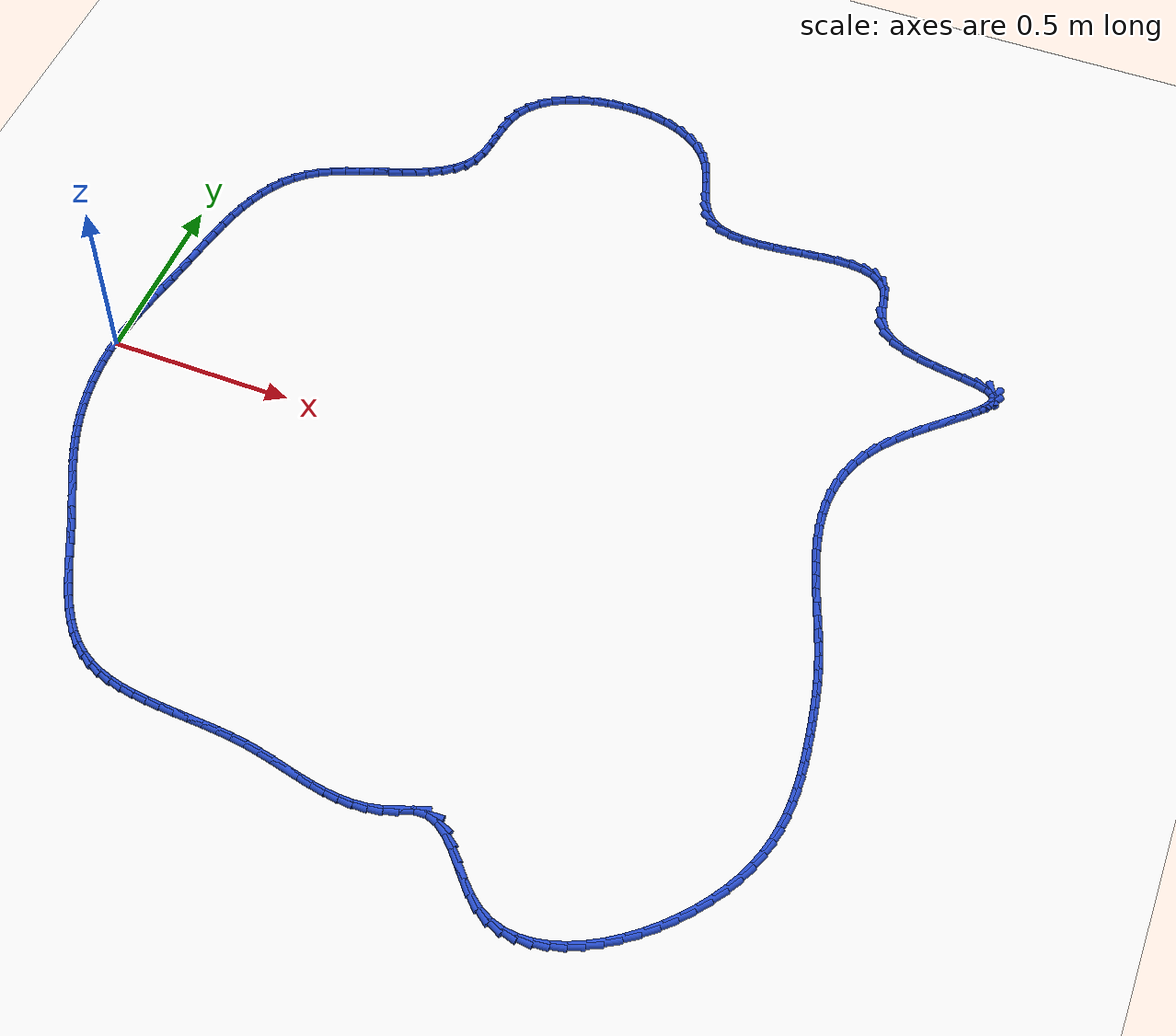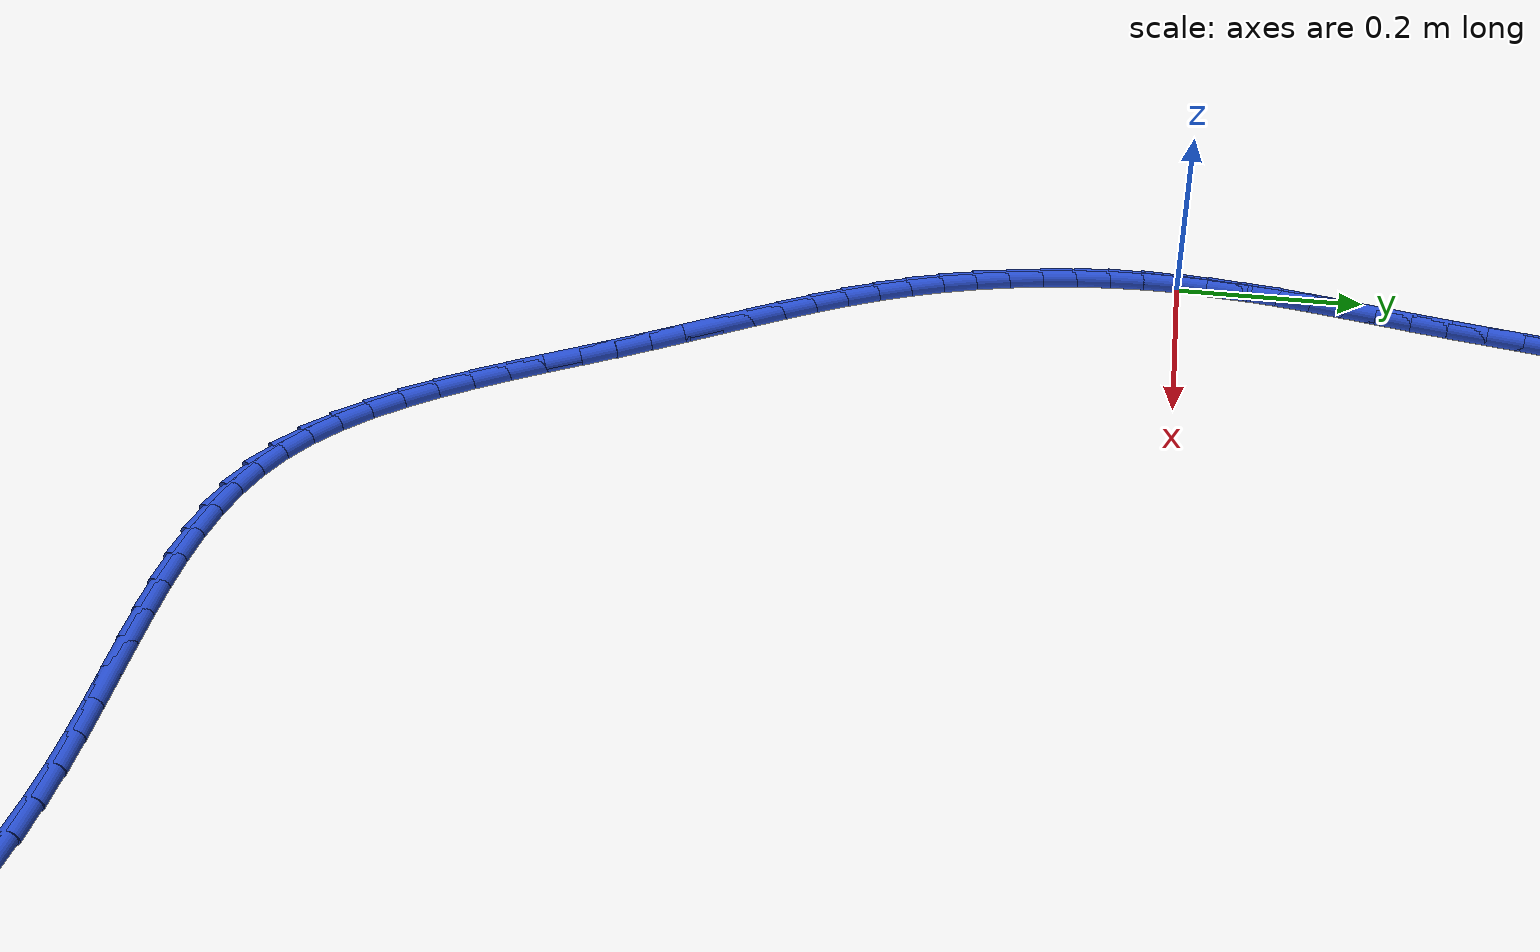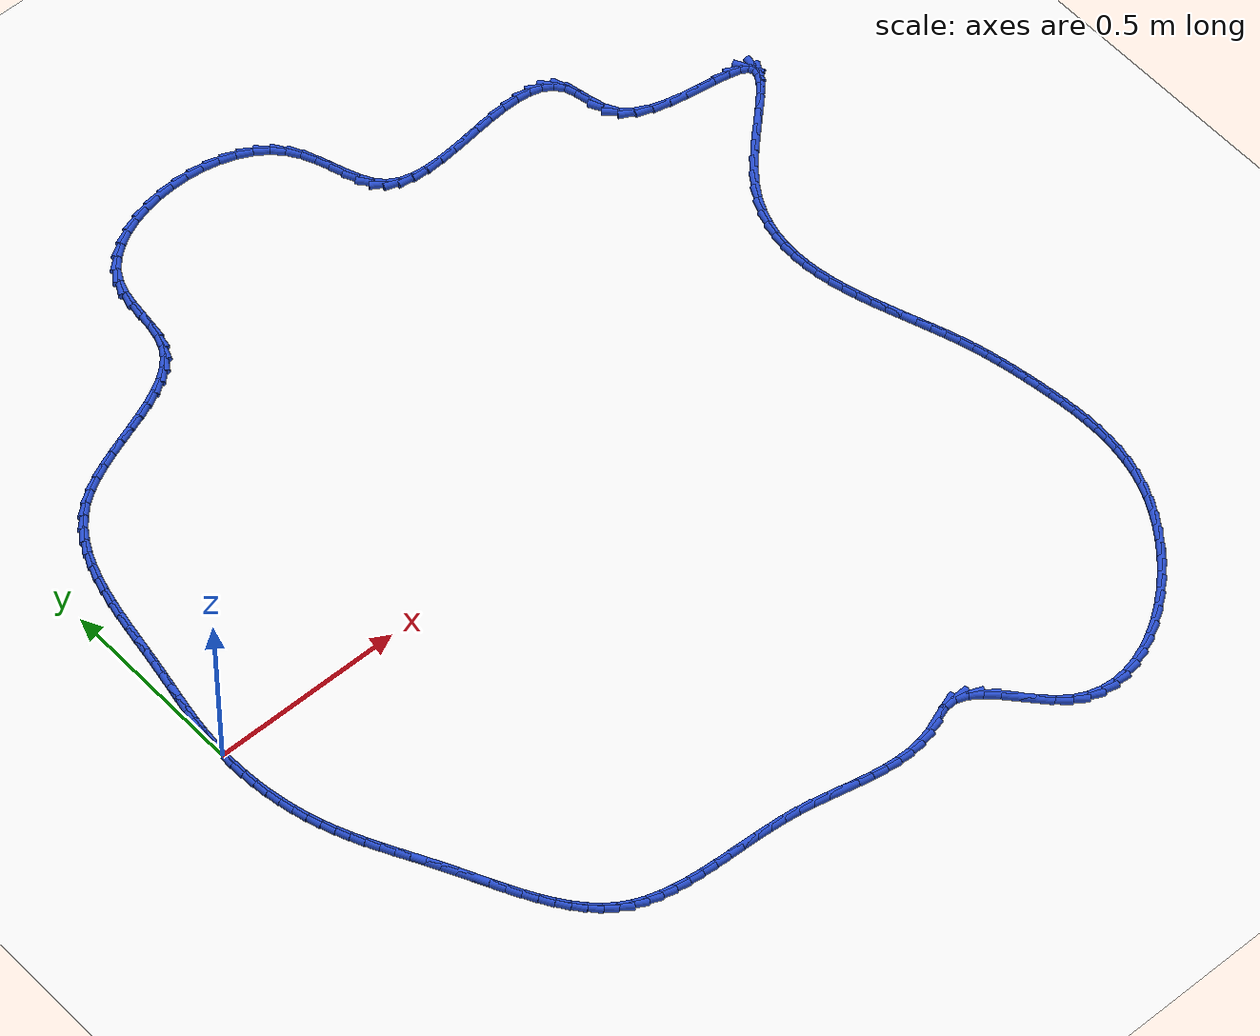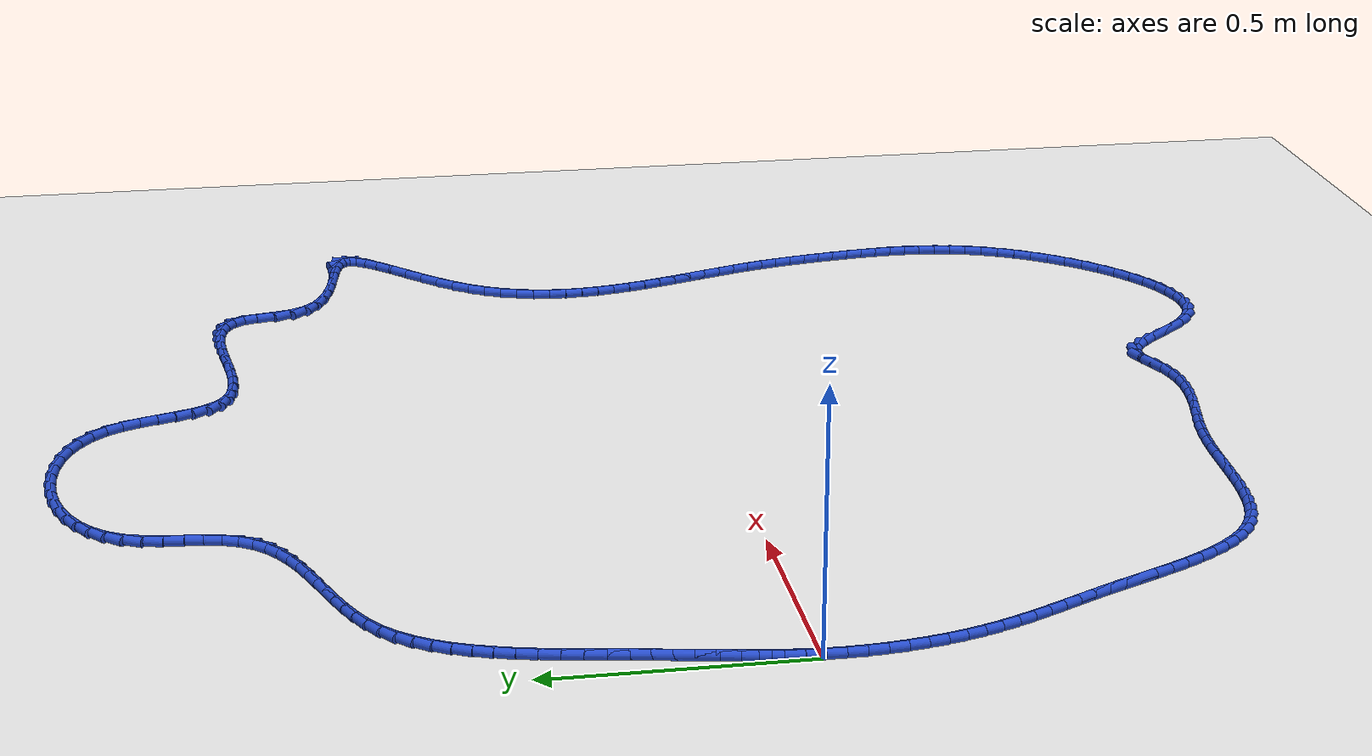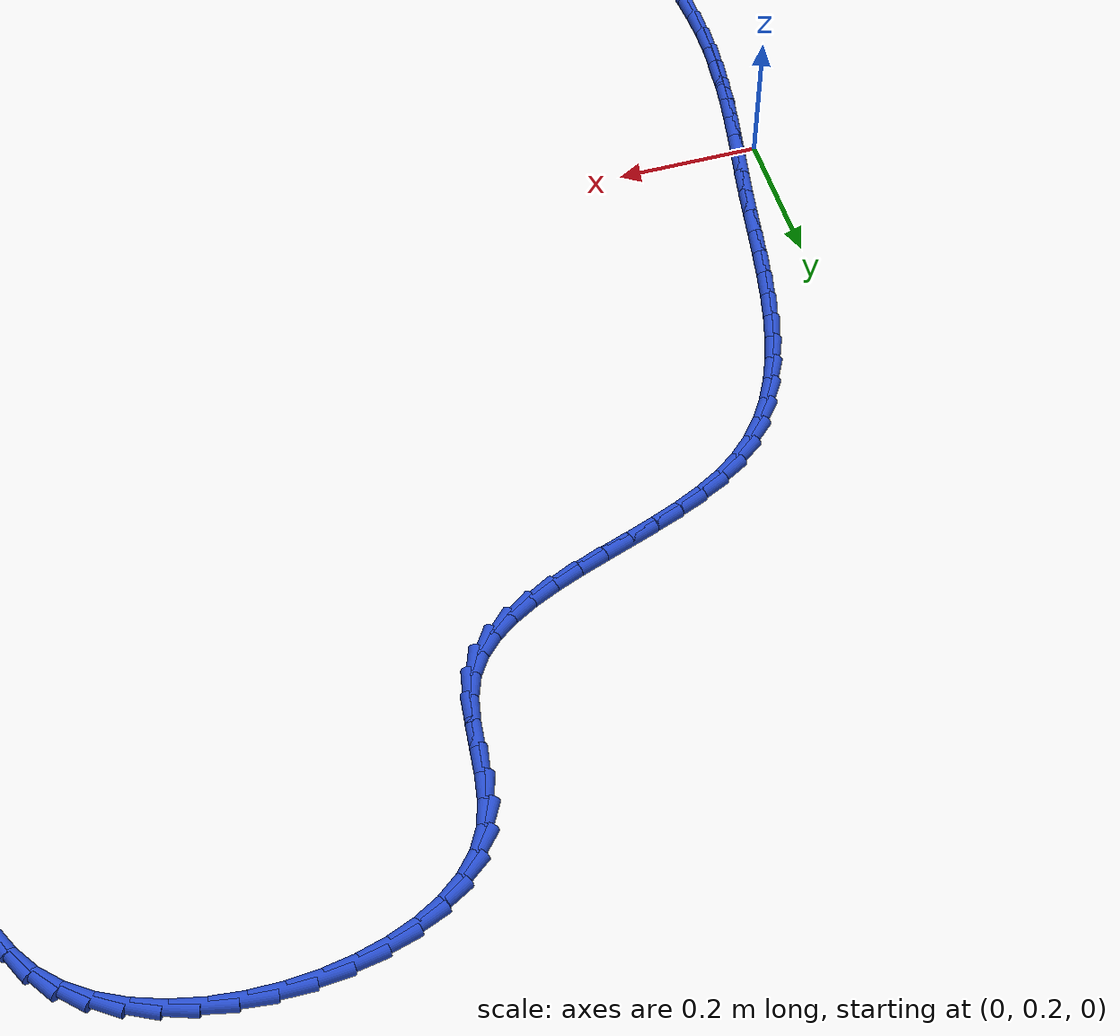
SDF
<sdf version="1.6">
 <world name="default">
  <light name="sun" type="directional">
   <pose>0 0 10 0 -0 0</pose>
   <diffuse>0.8 0.8 0.8 1</diffuse>
   <specular>0.2 0.2 0.2 1</specular>
   <attenuation>
    <range>1000</range>
    <constant>0.9</constant>
    <linear>0.01</linear>
    <quadratic>0.001</quadratic>
   </attenuation>
   <direction>-0.5 0.1 -0.9</direction>
  </light>
  <model name="ground_plane">
   <static>1</static>
   <link name="link">
    <collision name="collision">
     <geometry><plane><normal>0 0 1</normal><size>100 100</size></plane></geometry>
     <surface><friction><ode><mu>100</mu><mu2>50</mu2></ode></friction></surface>
    </collision>
    <visual name="visual">
     <cast_shadows>0</cast_shadows>
     <geometry><plane><normal>0 0 1</normal><size>100 100</size></plane></geometry>
     <material>
      <script><uri>file://media/materials/scripts/gazebo.material</uri><name>Gazebo/WhiteGlow</name></script>
     </material>
    </visual>
   </link>
  </model>
  <gravity>0 0 -9.8</gravity>
  <magnetic_field>6e-06 2.3e-05 -4.2e-05</magnetic_field>
  <atmosphere type="adiabatic"/>
  <physics name="default_physics" default="0" type="ode">
   <max_step_size>0.001</max_step_size>
   <real_time_factor>1</real_time_factor>
   <real_time_update_rate>1000</real_time_update_rate>
  </physics>
  <scene><ambient>0.4 0.4 0.4 1</ambient><background>0.7 0.7 0.7 1</background><shadows>1</shadows></scene>
  <spherical_coordinates>
   <surface_model>EARTH_WGS84</surface_model>
   <latitude_deg>0</latitude_deg>
   <longitude_deg>0</longitude_deg>
   <elevation>0</elevation>
   <heading_deg>0</heading_deg>
  </spherical_coordinates>
  <model name="line">
   <link name="link_0">
    <pose>1.9081958235744878e-17 7.632783294297951e-17 0.01 0 1.57 1.5107125301188573</pose>
    <collision name="collision">
     <geometry><cylinder><radius>0.01</radius><length>0.08</length></cylinder></geometry>
    </collision>
    <visual name="visual">
     <material>
      <script><name>Gazebo/Blue</name><uri>file://media/materials/scripts/gazebo.material</uri></script>
     </material>
     <geometry><cylinder><radius>0.01</radius><length>0.08</length></cylinder></geometry>
    </visual>
   </link>
   <link name="link_1">
    <pose>0.0021696803780791364 0.03606744206211067 0.01 0 1.57 1.4698358230574256</pose>
    <collision name="collision">
     <geometry><cylinder><radius>0.01</radius><length>0.08</length></cylinder></geometry>
    </collision>
    <visual name="visual">
     <material>
      <script><name>Gazebo/Blue</name><uri>file://media/materials/scripts/gazebo.material</uri></script>
     </material>
     <geometry><cylinder><radius>0.01</radius><length>0.08</length></cylinder></geometry>
    </visual>
   </link>
   <link name="link_2">
    <pose>0.005795411700264697 0.07185771404397197 0.01 0 1.57 1.4364751229464514</pose>
    <collision name="collision">
     <geometry><cylinder><radius>0.01</radius><length>0.08</length></cylinder></geometry>
    </collision>
    <visual name="visual">
     <material>
      <script><name>Gazebo/Blue</name><uri>file://media/materials/scripts/gazebo.material</uri></script>
     </material>
     <geometry><cylinder><radius>0.01</radius><length>0.08</length></cylinder></geometry>
    </visual>
   </link>
   <link name="link_3">
    <pose>0.010614170161304264 0.10751659063302756 0.01 0 1.57 1.4110195175571607</pose>
    <collision name="collision">
     <geometry><cylinder><radius>0.01</radius><length>0.08</length></cylinder></geometry>
    </collision>
    <visual name="visual">
     <material>
      <script><name>Gazebo/Blue</name><uri>file://media/materials/scripts/gazebo.material</uri></script>
     </material>
     <geometry><cylinder><radius>0.01</radius><length>0.08</length></cylinder></geometry>
    </visual>
   </link>
   <link name="link_4">
    <pose>0.016362931955945417 0.14318984651672112 0.01 0 1.57 1.3936299652264368</pose>
    <collision name="collision">
     <geometry><cylinder><radius>0.01</radius><length>0.08</length></cylinder></geometry>
    </collision>
    <visual name="visual">
     <material>
      <script><name>Gazebo/Blue</name><uri>file://media/materials/scripts/gazebo.material</uri></script>
     </material>
     <geometry><cylinder><radius>0.01</radius><length>0.08</length></cylinder></geometry>
    </visual>
   </link>
   <link name="link_5">
    <pose>0.02277867327893572 0.1790232563824962 0.01 0 1.57 1.3842839368484852</pose>
    <collision name="collision">
     <geometry><cylinder><radius>0.01</radius><length>0.08</length></cylinder></geometry>
    </collision>
    <visual name="visual">
     <material>
      <script><name>Gazebo/Blue</name><uri>file://media/materials/scripts/gazebo.material</uri></script>
     </material>
     <geometry><cylinder><radius>0.01</radius><length>0.08</length></cylinder></geometry>
    </visual>
   </link>
   <link name="link_6">
    <pose>0.029598370325022758 0.2151625949177964 0.01 0 1.57 1.3828146434916295</pose>
    <collision name="collision">
     <geometry><cylinder><radius>0.01</radius><length>0.08</length></cylinder></geometry>
    </collision>
    <visual name="visual">
     <material>
      <script><name>Gazebo/Blue</name><uri>file://media/materials/scripts/gazebo.material</uri></script>
     </material>
     <geometry><cylinder><radius>0.01</radius><length>0.08</length></cylinder></geometry>
    </visual>
   </link>
   <link name="link_7">
    <pose>0.03655899928895408 0.2517536368100654 0.01 0 1.57 1.3889395975615912</pose>
    <collision name="collision">
     <geometry><cylinder><radius>0.01</radius><length>0.08</length></cylinder></geometry>
    </collision>
    <visual name="visual">
     <material>
      <script><name>Gazebo/Blue</name><uri>file://media/materials/scripts/gazebo.material</uri></script>
     </material>
     <geometry><cylinder><radius>0.01</radius><length>0.08</length></cylinder></geometry>
    </visual>
   </link>
   <link name="link_8">
    <pose>0.043397536365477274 0.28894215674674684 0.01 0 1.57 1.4005665244814194</pose>
    <collision name="collision">
     <geometry><cylinder><radius>0.01</radius><length>0.08</length></cylinder></geometry>
    </collision>
    <visual name="visual">
     <material>
      <script><name>Gazebo/Blue</name><uri>file://media/materials/scripts/gazebo.material</uri></script>
     </material>
     <geometry><cylinder><radius>0.01</radius><length>0.08</length></cylinder></geometry>
    </visual>
   </link>
   <link name="link_9">
    <pose>0.04991006792208452 0.3268291923162857 0.01 0 1.57 1.4066362405724966</pose>
    <collision name="collision">
     <geometry><cylinder><radius>0.01</radius><length>0.08</length></cylinder></geometry>
    </collision>
    <visual name="visual">
     <material>
      <script><name>Gazebo/Blue</name><uri>file://media/materials/scripts/gazebo.material</uri></script>
     </material>
     <geometry><cylinder><radius>0.01</radius><length>0.08</length></cylinder></geometry>
    </visual>
   </link>
   <link name="link_10">
    <pose>0.05627108980315464 0.3652293846808706 0.01 0 1.57 1.403196595726689</pose>
    <collision name="collision">
     <geometry><cylinder><radius>0.01</radius><length>0.08</length></cylinder></geometry>
    </collision>
    <visual name="visual">
     <material>
      <script><name>Gazebo/Blue</name><uri>file://media/materials/scripts/gazebo.material</uri></script>
     </material>
     <geometry><cylinder><radius>0.01</radius><length>0.08</length></cylinder></geometry>
    </visual>
   </link>
   <link name="link_11">
    <pose>0.06280425663752094 0.40384448527496924 0.01 0 1.57 1.390349921122728</pose>
    <collision name="collision">
     <geometry><cylinder><radius>0.01</radius><length>0.08</length></cylinder></geometry>
    </collision>
    <visual name="visual">
     <material>
      <script><name>Gazebo/Blue</name><uri>file://media/materials/scripts/gazebo.material</uri></script>
     </material>
     <geometry><cylinder><radius>0.01</radius><length>0.08</length></cylinder></geometry>
    </visual>
   </link>
   <link name="link_12">
    <pose>0.06983358477151644 0.4423759717698235 0.01 0 1.57 1.3678711176888354</pose>
    <collision name="collision">
     <geometry><cylinder><radius>0.01</radius><length>0.08</length></cylinder></geometry>
    </collision>
    <visual name="visual">
     <material>
      <script><name>Gazebo/Blue</name><uri>file://media/materials/scripts/gazebo.material</uri></script>
     </material>
     <geometry><cylinder><radius>0.01</radius><length>0.08</length></cylinder></geometry>
    </visual>
   </link>
   <link name="link_13">
    <pose>0.07768309055147422 0.48052532183667507 0.01 0 1.57 1.3352207141225851</pose>
    <collision name="collision">
     <geometry><cylinder><radius>0.01</radius><length>0.08</length></cylinder></geometry>
    </collision>
    <visual name="visual">
     <material>
      <script><name>Gazebo/Blue</name><uri>file://media/materials/scripts/gazebo.material</uri></script>
     </material>
     <geometry><cylinder><radius>0.01</radius><length>0.08</length></cylinder></geometry>
    </visual>
   </link>
   <link name="link_14">
    <pose>0.08667679032372737 0.5179940131467659 0.01 0 1.57 1.2915762773624162</pose>
    <collision name="collision">
     <geometry><cylinder><radius>0.01</radius><length>0.08</length></cylinder></geometry>
    </collision>
    <visual name="visual">
     <material>
      <script><name>Gazebo/Blue</name><uri>file://media/materials/scripts/gazebo.material</uri></script>
     </material>
     <geometry><cylinder><radius>0.01</radius><length>0.08</length></cylinder></geometry>
    </visual>
   </link>
   <link name="link_15">
    <pose>0.09713870043460894 0.5544835233713372 0.01 0 1.57 1.235893511893885</pose>
    <collision name="collision">
     <geometry><cylinder><radius>0.01</radius><length>0.08</length></cylinder></geometry>
    </collision>
    <visual name="visual">
     <material>
      <script><name>Gazebo/Blue</name><uri>file://media/materials/scripts/gazebo.material</uri></script>
     </material>
     <geometry><cylinder><radius>0.01</radius><length>0.08</length></cylinder></geometry>
    </visual>
   </link>
   <link name="link_16">
    <pose>0.10939283723045201 0.5896953301816312 0.01 0 1.57 1.1670320679558441</pose>
    <collision name="collision">
     <geometry><cylinder><radius>0.01</radius><length>0.08</length></cylinder></geometry>
    </collision>
    <visual name="visual">
     <material>
      <script><name>Gazebo/Blue</name><uri>file://media/materials/scripts/gazebo.material</uri></script>
     </material>
     <geometry><cylinder><radius>0.01</radius><length>0.08</length></cylinder></geometry>
    </visual>
   </link>
   <link name="link_17">
    <pose>0.1237632170575896 0.6233309112488893 0.01 0 1.57 1.0839934890728224</pose>
    <collision name="collision">
     <geometry><cylinder><radius>0.01</radius><length>0.08</length></cylinder></geometry>
    </collision>
    <visual name="visual">
     <material>
      <script><name>Gazebo/Blue</name><uri>file://media/materials/scripts/gazebo.material</uri></script>
     </material>
     <geometry><cylinder><radius>0.01</radius><length>0.08</length></cylinder></geometry>
    </visual>
   </link>
   <link name="link_18">
    <pose>0.14057385626235486 0.6550917442443535 0.01 0 1.57 0.9863147120510044</pose>
    <collision name="collision">
     <geometry><cylinder><radius>0.01</radius><length>0.08</length></cylinder></geometry>
    </collision>
    <visual name="visual">
     <material>
      <script><name>Gazebo/Blue</name><uri>file://media/materials/scripts/gazebo.material</uri></script>
     </material>
     <geometry><cylinder><radius>0.01</radius><length>0.08</length></cylinder></geometry>
    </visual>
   </link>
   <link name="link_19">
    <pose>0.1601487711910809 0.6846793068392655 0.01 0 1.57 0.8746074095480045</pose>
    <collision name="collision">
     <geometry><cylinder><radius>0.01</radius><length>0.08</length></cylinder></geometry>
    </collision>
    <visual name="visual">
     <material>
      <script><name>Gazebo/Blue</name><uri>file://media/materials/scripts/gazebo.material</uri></script>
     </material>
     <geometry><cylinder><radius>0.01</radius><length>0.08</length></cylinder></geometry>
    </visual>
   </link>
   <link name="link_20">
    <pose>0.1828119781901006 0.7117950767048666 0.01 0 1.57 0.7510992967602634</pose>
    <collision name="collision">
     <geometry><cylinder><radius>0.01</radius><length>0.08</length></cylinder></geometry>
    </collision>
    <visual name="visual">
     <material>
      <script><name>Gazebo/Blue</name><uri>file://media/materials/scripts/gazebo.material</uri></script>
     </material>
     <geometry><cylinder><radius>0.01</radius><length>0.08</length></cylinder></geometry>
    </visual>
   </link>
   <link name="link_21">
    <pose>0.20888749360574713 0.736140531512399 0.01 0 1.57 0.6222709550161053</pose>
    <collision name="collision">
     <geometry><cylinder><radius>0.01</radius><length>0.08</length></cylinder></geometry>
    </collision>
    <visual name="visual">
     <material>
      <script><name>Gazebo/Blue</name><uri>file://media/materials/scripts/gazebo.material</uri></script>
     </material>
     <geometry><cylinder><radius>0.01</radius><length>0.08</length></cylinder></geometry>
    </visual>
   </link>
   <link name="link_22">
    <pose>0.23862778836562093 0.7574745226942908 0.01 0 1.57 0.513608327752599</pose>
    <collision name="collision">
     <geometry><cylinder><radius>0.01</radius><length>0.08</length></cylinder></geometry>
    </collision>
    <visual name="visual">
     <material>
      <script><name>Gazebo/Blue</name><uri>file://media/materials/scripts/gazebo.material</uri></script>
     </material>
     <geometry><cylinder><radius>0.01</radius><length>0.08</length></cylinder></geometry>
    </visual>
   </link>
   <link name="link_23">
    <pose>0.27162280484067824 0.7760871971294381 0.01 0 1.57 0.434576114114697</pose>
    <collision name="collision">
     <geometry><cylinder><radius>0.01</radius><length>0.08</length></cylinder></geometry>
    </collision>
    <visual name="visual">
     <material>
      <script><name>Gazebo/Blue</name><uri>file://media/materials/scripts/gazebo.material</uri></script>
     </material>
     <geometry><cylinder><radius>0.01</radius><length>0.08</length></cylinder></geometry>
    </visual>
   </link>
   <link name="link_24">
    <pose>0.3071037060225946 0.7925564143524177 0.01 0 1.57 0.3811711112654651</pose>
    <collision name="collision">
     <geometry><cylinder><radius>0.01</radius><length>0.08</length></cylinder></geometry>
    </collision>
    <visual name="visual">
     <material>
      <script><name>Gazebo/Blue</name><uri>file://media/materials/scripts/gazebo.material</uri></script>
     </material>
     <geometry><cylinder><radius>0.01</radius><length>0.08</length></cylinder></geometry>
    </visual>
   </link>
   <link name="link_25">
    <pose>0.3442981206101238 0.8074628681209044 0.01 0 1.57 0.35008837016153826</pose>
    <collision name="collision">
     <geometry><cylinder><radius>0.01</radius><length>0.08</length></cylinder></geometry>
    </collision>
    <visual name="visual">
     <material>
      <script><name>Gazebo/Blue</name><uri>file://media/materials/scripts/gazebo.material</uri></script>
     </material>
     <geometry><cylinder><radius>0.01</radius><length>0.08</length></cylinder></geometry>
    </visual>
   </link>
   <link name="link_26">
    <pose>0.38243367730201894 0.8213872521925707 0.01 0 1.57 0.3393816111067285</pose>
    <collision name="collision">
     <geometry><cylinder><radius>0.01</radius><length>0.08</length></cylinder></geometry>
    </collision>
    <visual name="visual">
     <material>
      <script><name>Gazebo/Blue</name><uri>file://media/materials/scripts/gazebo.material</uri></script>
     </material>
     <geometry><cylinder><radius>0.01</radius><length>0.08</length></cylinder></geometry>
    </visual>
   </link>
   <link name="link_27">
    <pose>0.42073800479703355 0.8349102603250897 0.01 0 1.57 0.3486063184376379</pose>
    <collision name="collision">
     <geometry><cylinder><radius>0.01</radius><length>0.08</length></cylinder></geometry>
    </collision>
    <visual name="visual">
     <material>
      <script><name>Gazebo/Blue</name><uri>file://media/materials/scripts/gazebo.material</uri></script>
     </material>
     <geometry><cylinder><radius>0.01</radius><length>0.08</length></cylinder></geometry>
    </visual>
   </link>
   <link name="link_28">
    <pose>0.45843873179392075 0.8486125862761349 0.01 0 1.57 0.37890188908485356</pose>
    <collision name="collision">
     <geometry><cylinder><radius>0.01</radius><length>0.08</length></cylinder></geometry>
    </collision>
    <visual name="visual">
     <material>
      <script><name>Gazebo/Blue</name><uri>file://media/materials/scripts/gazebo.material</uri></script>
     </material>
     <geometry><cylinder><radius>0.01</radius><length>0.08</length></cylinder></geometry>
    </visual>
   </link>
   <link name="link_29">
    <pose>0.4947634869914337 0.8630749238033795 0.01 0 1.57 0.4331146506210727</pose>
    <collision name="collision">
     <geometry><cylinder><radius>0.01</radius><length>0.08</length></cylinder></geometry>
    </collision>
    <visual name="visual">
     <material>
      <script><name>Gazebo/Blue</name><uri>file://media/materials/scripts/gazebo.material</uri></script>
     </material>
     <geometry><cylinder><radius>0.01</radius><length>0.08</length></cylinder></geometry>
    </visual>
   </link>
   <link name="link_30">
    <pose>0.5289398990883263 0.8788779666644964 0.01 0 1.57 0.5158608734634753</pose>
    <collision name="collision">
     <geometry><cylinder><radius>0.01</radius><length>0.08</length></cylinder></geometry>
    </collision>
    <visual name="visual">
     <material>
      <script><name>Gazebo/Blue</name><uri>file://media/materials/scripts/gazebo.material</uri></script>
     </material>
     <geometry><cylinder><radius>0.01</radius><length>0.08</length></cylinder></geometry>
    </visual>
   </link>
   <link name="link_31">
    <pose>0.560195596783351 0.8966024086171589 0.01 0 1.57 0.6330779431743189</pose>
    <collision name="collision">
     <geometry><cylinder><radius>0.01</radius><length>0.08</length></cylinder></geometry>
    </collision>
    <visual name="visual">
     <material>
      <script><name>Gazebo/Blue</name><uri>file://media/materials/scripts/gazebo.material</uri></script>
     </material>
     <geometry><cylinder><radius>0.01</radius><length>0.08</length></cylinder></geometry>
    </visual>
   </link>
   <link name="link_32">
    <pose>0.5877582087752621 0.9168289434190408 0.01 0 1.57 0.7899700455883676</pose>
    <collision name="collision">
     <geometry><cylinder><radius>0.01</radius><length>0.08</length></cylinder></geometry>
    </collision>
    <visual name="visual">
     <material>
      <script><name>Gazebo/Blue</name><uri>file://media/materials/scripts/gazebo.material</uri></script>
     </material>
     <geometry><cylinder><radius>0.01</radius><length>0.08</length></cylinder></geometry>
    </visual>
   </link>
   <link name="link_33">
    <pose>0.6108553637628124 0.9401382648278145 0.01 0 1.57 0.9859455712762099</pose>
    <collision name="collision">
     <geometry><cylinder><radius>0.01</radius><length>0.08</length></cylinder></geometry>
    </collision>
    <visual name="visual">
     <material>
      <script><name>Gazebo/Blue</name><uri>file://media/materials/scripts/gazebo.material</uri></script>
     </material>
     <geometry><cylinder><radius>0.01</radius><length>0.08</length></cylinder></geometry>
    </visual>
   </link>
   <link name="link_34">
    <pose>0.6287146904447549 0.9671110666011533 0.01 0 1.57 1.2044139987612823</pose>
    <collision name="collision">
     <geometry><cylinder><radius>0.01</radius><length>0.08</length></cylinder></geometry>
    </collision>
    <visual name="visual">
     <material>
      <script><name>Gazebo/Blue</name><uri>file://media/materials/scripts/gazebo.material</uri></script>
     </material>
     <geometry><cylinder><radius>0.01</radius><length>0.08</length></cylinder></geometry>
    </visual>
   </link>
   <link name="link_35">
    <pose>0.6406674823394365 0.9982618919987081 0.01 0 1.57 1.3708400819970343</pose>
    <collision name="collision">
     <geometry><cylinder><radius>0.01</radius><length>0.08</length></cylinder></geometry>
    </collision>
    <visual name="visual">
     <material>
      <script><name>Gazebo/Blue</name><uri>file://media/materials/scripts/gazebo.material</uri></script>
     </material>
     <geometry><cylinder><radius>0.01</radius><length>0.08</length></cylinder></geometry>
    </visual>
   </link>
   <link name="link_36">
    <pose>0.647715618034429 1.0330392520933838 0.01 0 1.57 1.44986373121103</pose>
    <collision name="collision">
     <geometry><cylinder><radius>0.01</radius><length>0.08</length></cylinder></geometry>
    </collision>
    <visual name="visual">
     <material>
      <script><name>Gazebo/Blue</name><uri>file://media/materials/scripts/gazebo.material</uri></script>
     </material>
     <geometry><cylinder><radius>0.01</radius><length>0.08</length></cylinder></geometry>
    </visual>
   </link>
   <link name="link_37">
    <pose>0.6522109656071282 1.0700302039235514 0.01 0 1.57 1.456564288502031</pose>
    <collision name="collision">
     <geometry><cylinder><radius>0.01</radius><length>0.08</length></cylinder></geometry>
    </collision>
    <visual name="visual">
     <material>
      <script><name>Gazebo/Blue</name><uri>file://media/materials/scripts/gazebo.material</uri></script>
     </material>
     <geometry><cylinder><radius>0.01</radius><length>0.08</length></cylinder></geometry>
    </visual>
   </link>
   <link name="link_38">
    <pose>0.6565440248854156 1.1077971528709811 0.01 0 1.57 1.3957773819081913</pose>
    <collision name="collision">
     <geometry><cylinder><radius>0.01</radius><length>0.08</length></cylinder></geometry>
    </collision>
    <visual name="visual">
     <material>
      <script><name>Gazebo/Blue</name><uri>file://media/materials/scripts/gazebo.material</uri></script>
     </material>
     <geometry><cylinder><radius>0.01</radius><length>0.08</length></cylinder></geometry>
    </visual>
   </link>
   <link name="link_39">
    <pose>0.6631052956971728 1.144902504317443 0.01 0 1.57 1.2616632803875663</pose>
    <collision name="collision">
     <geometry><cylinder><radius>0.01</radius><length>0.08</length></cylinder></geometry>
    </collision>
    <visual name="visual">
     <material>
      <script><name>Gazebo/Blue</name><uri>file://media/materials/scripts/gazebo.material</uri></script>
     </material>
     <geometry><cylinder><radius>0.01</radius><length>0.08</length></cylinder></geometry>
    </visual>
   </link>
   <link name="link_40">
    <pose>0.6742852778702814 1.179908663644708 0.01 0 1.57 1.0561876570562012</pose>
    <collision name="collision">
     <geometry><cylinder><radius>0.01</radius><length>0.08</length></cylinder></geometry>
    </collision>
    <visual name="visual">
     <material>
      <script><name>Gazebo/Blue</name><uri>file://media/materials/scripts/gazebo.material</uri></script>
     </material>
     <geometry><cylinder><radius>0.01</radius><length>0.08</length></cylinder></geometry>
    </visual>
   </link>
   <link name="link_41">
    <pose>0.6921539661439563 1.2115108869189446 0.01 0 1.57 0.8478943375363157</pose>
    <collision name="collision">
     <geometry><cylinder><radius>0.01</radius><length>0.08</length></cylinder></geometry>
    </collision>
    <visual name="visual">
     <material>
      <script><name>Gazebo/Blue</name><uri>file://media/materials/scripts/gazebo.material</uri></script>
     </material>
     <geometry><cylinder><radius>0.01</radius><length>0.08</length></cylinder></geometry>
    </visual>
   </link>
   <link name="link_42">
    <pose>0.7166567812597245 1.23928507491253 0.01 0 1.57 0.6687808550829932</pose>
    <collision name="collision">
     <geometry><cylinder><radius>0.01</radius><length>0.08</length></cylinder></geometry>
    </collision>
    <visual name="visual">
     <material>
      <script><name>Gazebo/Blue</name><uri>file://media/materials/scripts/gazebo.material</uri></script>
     </material>
     <geometry><cylinder><radius>0.01</radius><length>0.08</length></cylinder></geometry>
    </visual>
   </link>
   <link name="link_43">
    <pose>0.7468747018690478 1.2631654432182597 0.01 0 1.57 0.5173192038806435</pose>
    <collision name="collision">
     <geometry><cylinder><radius>0.01</radius><length>0.08</length></cylinder></geometry>
    </collision>
    <visual name="visual">
     <material>
      <script><name>Gazebo/Blue</name><uri>file://media/materials/scripts/gazebo.material</uri></script>
     </material>
     <geometry><cylinder><radius>0.01</radius><length>0.08</length></cylinder></geometry>
    </visual>
   </link>
   <link name="link_44">
    <pose>0.781886193053816 1.2830872493139078 0.01 0 1.57 0.3881337335708626</pose>
    <collision name="collision">
     <geometry><cylinder><radius>0.01</radius><length>0.08</length></cylinder></geometry>
    </collision>
    <visual name="visual">
     <material>
      <script><name>Gazebo/Blue</name><uri>file://media/materials/scripts/gazebo.material</uri></script>
     </material>
     <geometry><cylinder><radius>0.01</radius><length>0.08</length></cylinder></geometry>
    </visual>
   </link>
   <link name="link_45">
    <pose>0.8207697198959191 1.2989857506772475 0.01 0 1.57 0.27515589376207744</pose>
    <collision name="collision">
     <geometry><cylinder><radius>0.01</radius><length>0.08</length></cylinder></geometry>
    </collision>
    <visual name="visual">
     <material>
      <script><name>Gazebo/Blue</name><uri>file://media/materials/scripts/gazebo.material</uri></script>
     </material>
     <geometry><cylinder><radius>0.01</radius><length>0.08</length></cylinder></geometry>
    </visual>
   </link>
   <link name="link_46">
    <pose>0.8626037474772476 1.3107962047860542 0.01 0 1.57 0.17283951026834776</pose>
    <collision name="collision">
     <geometry><cylinder><radius>0.01</radius><length>0.08</length></cylinder></geometry>
    </collision>
    <visual name="visual">
     <material>
      <script><name>Gazebo/Blue</name><uri>file://media/materials/scripts/gazebo.material</uri></script>
     </material>
     <geometry><cylinder><radius>0.01</radius><length>0.08</length></cylinder></geometry>
    </visual>
   </link>
   <link name="link_47">
    <pose>0.9064667408796909 1.3184538691181007 0.01 0 1.57 0.0763489587434544</pose>
    <collision name="collision">
     <geometry><cylinder><radius>0.01</radius><length>0.08</length></cylinder></geometry>
    </collision>
    <visual name="visual">
     <material>
      <script><name>Gazebo/Blue</name><uri>file://media/materials/scripts/gazebo.material</uri></script>
     </material>
     <geometry><cylinder><radius>0.01</radius><length>0.08</length></cylinder></geometry>
    </visual>
   </link>
   <link name="link_48">
    <pose>0.9514371651851397 1.3218940011511615 0.01 0 1.57 -0.01864733817116636</pose>
    <collision name="collision">
     <geometry><cylinder><radius>0.01</radius><length>0.08</length></cylinder></geometry>
    </collision>
    <visual name="visual">
     <material>
      <script><name>Gazebo/Blue</name><uri>file://media/materials/scripts/gazebo.material</uri></script>
     </material>
     <geometry><cylinder><radius>0.01</radius><length>0.08</length></cylinder></geometry>
    </visual>
   </link>
   <link name="link_49">
    <pose>0.9965934854754843 1.3210518583630115 0.01 0 1.57 -0.11629148016576486</pose>
    <collision name="collision">
     <geometry><cylinder><radius>0.01</radius><length>0.08</length></cylinder></geometry>
    </collision>
    <visual name="visual">
     <material>
      <script><name>Gazebo/Blue</name><uri>file://media/materials/scripts/gazebo.material</uri></script>
     </material>
     <geometry><cylinder><radius>0.01</radius><length>0.08</length></cylinder></geometry>
    </visual>
   </link>
   <link name="link_50">
    <pose>1.0410141668326138 1.3158626982314237 0.01 0 1.57 -0.22084989505280353</pose>
    <collision name="collision">
     <geometry><cylinder><radius>0.01</radius><length>0.08</length></cylinder></geometry>
    </collision>
    <visual name="visual">
     <material>
      <script><name>Gazebo/Blue</name><uri>file://media/materials/scripts/gazebo.material</uri></script>
     </material>
     <geometry><cylinder><radius>0.01</radius><length>0.08</length></cylinder></geometry>
    </visual>
   </link>
   <link name="link_51">
    <pose>1.0837776743384195 1.3062617782341728 0.01 0 1.57 -0.3369572909305993</pose>
    <collision name="collision">
     <geometry><cylinder><radius>0.01</radius><length>0.08</length></cylinder></geometry>
    </collision>
    <visual name="visual">
     <material>
      <script><name>Gazebo/Blue</name><uri>file://media/materials/scripts/gazebo.material</uri></script>
     </material>
     <geometry><cylinder><radius>0.01</radius><length>0.08</length></cylinder></geometry>
    </visual>
   </link>
   <link name="link_52">
    <pose>1.1239624730747908 1.2921843558490325 0.01 0 1.57 -0.4696568083055794</pose>
    <collision name="collision">
     <geometry><cylinder><radius>0.01</radius><length>0.08</length></cylinder></geometry>
    </collision>
    <visual name="visual">
     <material>
      <script><name>Gazebo/Blue</name><uri>file://media/materials/scripts/gazebo.material</uri></script>
     </material>
     <geometry><cylinder><radius>0.01</radius><length>0.08</length></cylinder></geometry>
    </visual>
   </link>
   <link name="link_53">
    <pose>1.1606470281236183 1.2735656885537767 0.01 0 1.57 -0.6239302826332535</pose>
    <collision name="collision">
     <geometry><cylinder><radius>0.01</radius><length>0.08</length></cylinder></geometry>
    </collision>
    <visual name="visual">
     <material>
      <script><name>Gazebo/Blue</name><uri>file://media/materials/scripts/gazebo.material</uri></script>
     </material>
     <geometry><cylinder><radius>0.01</radius><length>0.08</length></cylinder></geometry>
    </visual>
   </link>
   <link name="link_54">
    <pose>1.1929098045667912 1.25034103382618 0.01 0 1.57 -0.8032002500355849</pose>
    <collision name="collision">
     <geometry><cylinder><radius>0.01</radius><length>0.08</length></cylinder></geometry>
    </collision>
    <visual name="visual">
     <material>
      <script><name>Gazebo/Blue</name><uri>file://media/materials/scripts/gazebo.material</uri></script>
     </material>
     <geometry><cylinder><radius>0.01</radius><length>0.08</length></cylinder></geometry>
    </visual>
   </link>
   <link name="link_55">
    <pose>1.2198292674862001 1.2224456491440163 0.01 0 1.57 -0.9971599089499282</pose>
    <collision name="collision">
     <geometry><cylinder><radius>0.01</radius><length>0.08</length></cylinder></geometry>
    </collision>
    <visual name="visual">
     <material>
      <script><name>Gazebo/Blue</name><uri>file://media/materials/scripts/gazebo.material</uri></script>
     </material>
     <geometry><cylinder><radius>0.01</radius><length>0.08</length></cylinder></geometry>
    </visual>
   </link>
   <link name="link_56">
    <pose>1.2407832895362265 1.190014653340493 0.01 0 1.57 -1.1441190291686232</pose>
    <collision name="collision">
     <geometry><cylinder><radius>0.01</radius><length>0.08</length></cylinder></geometry>
    </collision>
    <visual name="visual">
     <material>
      <script><name>Gazebo/Blue</name><uri>file://media/materials/scripts/gazebo.material</uri></script>
     </material>
     <geometry><cylinder><radius>0.01</radius><length>0.08</length></cylinder></geometry>
    </visual>
   </link>
   <link name="link_57">
    <pose>1.2569736167109502 1.1544006421308444 0.01 0 1.57 -1.2252369603577207</pose>
    <collision name="collision">
     <geometry><cylinder><radius>0.01</radius><length>0.08</length></cylinder></geometry>
    </collision>
    <visual name="visual">
     <material>
      <script><name>Gazebo/Blue</name><uri>file://media/materials/scripts/gazebo.material</uri></script>
     </material>
     <geometry><cylinder><radius>0.01</radius><length>0.08</length></cylinder></geometry>
    </visual>
   </link>
   <link name="link_58">
    <pose>1.2702887396517943 1.1174146288812425 0.01 0 1.57 -1.2454152657191437</pose>
    <collision name="collision">
     <geometry><cylinder><radius>0.01</radius><length>0.08</length></cylinder></geometry>
    </collision>
    <visual name="visual">
     <material>
      <script><name>Gazebo/Blue</name><uri>file://media/materials/scripts/gazebo.material</uri></script>
     </material>
     <geometry><cylinder><radius>0.01</radius><length>0.08</length></cylinder></geometry>
    </visual>
   </link>
   <link name="link_59">
    <pose>1.2826183983591766 1.0808684609333672 0.01 0 1.57 -1.2025116066544055</pose>
    <collision name="collision">
     <geometry><cylinder><radius>0.01</radius><length>0.08</length></cylinder></geometry>
    </collision>
    <visual name="visual">
     <material>
      <script><name>Gazebo/Blue</name><uri>file://media/materials/scripts/gazebo.material</uri></script>
     </material>
     <geometry><cylinder><radius>0.01</radius><length>0.08</length></cylinder></geometry>
    </visual>
   </link>
   <link name="link_60">
    <pose>1.2958523328335143 1.0465739856288976 0.01 0 1.57 -1.0832943150114285</pose>
    <collision name="collision">
     <geometry><cylinder><radius>0.01</radius><length>0.08</length></cylinder></geometry>
    </collision>
    <visual name="visual">
     <material>
      <script><name>Gazebo/Blue</name><uri>file://media/materials/scripts/gazebo.material</uri></script>
     </material>
     <geometry><cylinder><radius>0.01</radius><length>0.08</length></cylinder></geometry>
    </visual>
   </link>
   <link name="link_61">
    <pose>1.3118802830752252 1.016343050309514 0.01 0 1.57 -0.8660760923200934</pose>
    <collision name="collision">
     <geometry><cylinder><radius>0.01</radius><length>0.08</length></cylinder></geometry>
    </collision>
    <visual name="visual">
     <material>
      <script><name>Gazebo/Blue</name><uri>file://media/materials/scripts/gazebo.material</uri></script>
     </material>
     <geometry><cylinder><radius>0.01</radius><length>0.08</length></cylinder></geometry>
    </visual>
   </link>
   <link name="link_62">
    <pose>1.3325919890847273 0.9919875023168959 0.01 0 1.57 -0.5657849297391847</pose>
    <collision name="collision">
     <geometry><cylinder><radius>0.01</radius><length>0.08</length></cylinder></geometry>
    </collision>
    <visual name="visual">
     <material>
      <script><name>Gazebo/Blue</name><uri>file://media/materials/scripts/gazebo.material</uri></script>
     </material>
     <geometry><cylinder><radius>0.01</radius><length>0.08</length></cylinder></geometry>
    </visual>
   </link>
   <link name="link_63">
    <pose>1.359479027373281 0.9749132180880576 0.01 0 1.57 -0.3082425800779235</pose>
    <collision name="collision">
     <geometry><cylinder><radius>0.01</radius><length>0.08</length></cylinder></geometry>
    </collision>
    <visual name="visual">
     <material>
      <script><name>Gazebo/Blue</name><uri>file://media/materials/scripts/gazebo.material</uri></script>
     </material>
     <geometry><cylinder><radius>0.01</radius><length>0.08</length></cylinder></geometry>
    </visual>
   </link>
   <link name="link_64">
    <pose>1.392078925475318 0.9645337089826356 0.01 0 1.57 -0.1302962452114974</pose>
    <collision name="collision">
     <geometry><cylinder><radius>0.01</radius><length>0.08</length></cylinder></geometry>
    </collision>
    <visual name="visual">
     <material>
      <script><name>Gazebo/Blue</name><uri>file://media/materials/scripts/gazebo.material</uri></script>
     </material>
     <geometry><cylinder><radius>0.01</radius><length>0.08</length></cylinder></geometry>
    </visual>
   </link>
   <link name="link_65">
    <pose>1.4293307414357517 0.9596522817415835 0.01 0 1.57 -0.014204694502514732</pose>
    <collision name="collision">
     <geometry><cylinder><radius>0.01</radius><length>0.08</length></cylinder></geometry>
    </collision>
    <visual name="visual">
     <material>
      <script><name>Gazebo/Blue</name><uri>file://media/materials/scripts/gazebo.material</uri></script>
     </material>
     <geometry><cylinder><radius>0.01</radius><length>0.08</length></cylinder></geometry>
    </visual>
   </link>
   <link name="link_66">
    <pose>1.4701733787565363 0.9590720855325297 0.01 0 1.57 0.058132410433115435</pose>
    <collision name="collision">
     <geometry><cylinder><radius>0.01</radius><length>0.08</length></cylinder></geometry>
    </collision>
    <visual name="visual">
     <material>
      <script><name>Gazebo/Blue</name><uri>file://media/materials/scripts/gazebo.material</uri></script>
     </material>
     <geometry><cylinder><radius>0.01</radius><length>0.08</length></cylinder></geometry>
    </visual>
   </link>
   <link name="link_67">
    <pose>1.5135457409396258 0.9615962695231034 0.01 0 1.57 0.09851183140055493</pose>
    <collision name="collision">
     <geometry><cylinder><radius>0.01</radius><length>0.08</length></cylinder></geometry>
    </collision>
    <visual name="visual">
     <material>
      <script><name>Gazebo/Blue</name><uri>file://media/materials/scripts/gazebo.material</uri></script>
     </material>
     <geometry><cylinder><radius>0.01</radius><length>0.08</length></cylinder></geometry>
    </visual>
   </link>
   <link name="link_68">
    <pose>1.5583867314869746 0.9660279828809333 0.01 0 1.57 0.11316220378862993</pose>
    <collision name="collision">
     <geometry><cylinder><radius>0.01</radius><length>0.08</length></cylinder></geometry>
    </collision>
    <visual name="visual">
     <material>
      <script><name>Gazebo/Blue</name><uri>file://media/materials/scripts/gazebo.material</uri></script>
     </material>
     <geometry><cylinder><radius>0.01</radius><length>0.08</length></cylinder></geometry>
    </visual>
   </link>
   <link name="link_69">
    <pose>1.6036352539005372 0.9711703747736475 0.01 0 1.57 0.1040343878712775</pose>
    <collision name="collision">
     <geometry><cylinder><radius>0.01</radius><length>0.08</length></cylinder></geometry>
    </collision>
    <visual name="visual">
     <material>
      <script><name>Gazebo/Blue</name><uri>file://media/materials/scripts/gazebo.material</uri></script>
     </material>
     <geometry><cylinder><radius>0.01</radius><length>0.08</length></cylinder></geometry>
    </visual>
   </link>
   <link name="link_70">
    <pose>1.6482302116822671 0.9758265943688758 0.01 0 1.57 0.06922632797128843</pose>
    <collision name="collision">
     <geometry><cylinder><radius>0.01</radius><length>0.08</length></cylinder></geometry>
    </collision>
    <visual name="visual">
     <material>
      <script><name>Gazebo/Blue</name><uri>file://media/materials/scripts/gazebo.material</uri></script>
     </material>
     <geometry><cylinder><radius>0.01</radius><length>0.08</length></cylinder></geometry>
    </visual>
   </link>
   <link name="link_71">
    <pose>1.6911105083341194 0.978799790834246 0.01 0 1.57 0.0023269768702133004</pose>
    <collision name="collision">
     <geometry><cylinder><radius>0.01</radius><length>0.08</length></cylinder></geometry>
    </collision>
    <visual name="visual">
     <material>
      <script><name>Gazebo/Blue</name><uri>file://media/materials/scripts/gazebo.material</uri></script>
     </material>
     <geometry><cylinder><radius>0.01</radius><length>0.08</length></cylinder></geometry>
    </visual>
   </link>
   <link name="link_72">
    <pose>1.7312150473580474 0.9788931133373868 0.01 0 1.57 -0.10939489236948147</pose>
    <collision name="collision">
     <geometry><cylinder><radius>0.01</radius><length>0.08</length></cylinder></geometry>
    </collision>
    <visual name="visual">
     <material>
      <script><name>Gazebo/Blue</name><uri>file://media/materials/scripts/gazebo.material</uri></script>
     </material>
     <geometry><cylinder><radius>0.01</radius><length>0.08</length></cylinder></geometry>
    </visual>
   </link>
   <link name="link_73">
    <pose>1.7674827322560065 0.9749097110459274 0.01 0 1.57 -0.28694857712832605</pose>
    <collision name="collision">
     <geometry><cylinder><radius>0.01</radius><length>0.08</length></cylinder></geometry>
    </collision>
    <visual name="visual">
     <material>
      <script><name>Gazebo/Blue</name><uri>file://media/materials/scripts/gazebo.material</uri></script>
     </material>
     <geometry><cylinder><radius>0.01</radius><length>0.08</length></cylinder></geometry>
    </visual>
   </link>
   <link name="link_74">
    <pose>1.79885246652995 0.9656527331274963 0.01 0 1.57 -0.5542215421288119</pose>
    <collision name="collision">
     <geometry><cylinder><radius>0.01</radius><length>0.08</length></cylinder></geometry>
    </collision>
    <visual name="visual">
     <material>
      <script><name>Gazebo/Blue</name><uri>file://media/materials/scripts/gazebo.material</uri></script>
     </material>
     <geometry><cylinder><radius>0.01</radius><length>0.08</length></cylinder></geometry>
    </visual>
   </link>
   <link name="link_75">
    <pose>1.8242631536818323 0.9499253287497226 0.01 0 1.57 -0.9045890638301629</pose>
    <collision name="collision">
     <geometry><cylinder><radius>0.01</radius><length>0.08</length></cylinder></geometry>
    </collision>
    <visual name="visual">
     <material>
      <script><name>Gazebo/Blue</name><uri>file://media/materials/scripts/gazebo.material</uri></script>
     </material>
     <geometry><cylinder><radius>0.01</radius><length>0.08</length></cylinder></geometry>
    </visual>
   </link>
   <link name="link_76">
    <pose>1.842653697213608 0.9265306470802339 0.01 0 1.57 -1.237732944576227</pose>
    <collision name="collision">
     <geometry><cylinder><radius>0.01</radius><length>0.08</length></cylinder></geometry>
    </collision>
    <visual name="visual">
     <material>
      <script><name>Gazebo/Blue</name><uri>file://media/materials/scripts/gazebo.material</uri></script>
     </material>
     <geometry><cylinder><radius>0.01</radius><length>0.08</length></cylinder></geometry>
    </visual>
   </link>
   <link name="link_77">
    <pose>1.853611738079482 0.8948555469258339 0.01 0 1.57 -1.3712552834792449</pose>
    <collision name="collision">
     <geometry><cylinder><radius>0.01</radius><length>0.08</length></cylinder></geometry>
    </collision>
    <visual name="visual">
     <material>
      <script><name>Gazebo/Blue</name><uri>file://media/materials/scripts/gazebo.material</uri></script>
     </material>
     <geometry><cylinder><radius>0.01</radius><length>0.08</length></cylinder></geometry>
    </visual>
   </link>
   <link name="link_78">
    <pose>1.861032261327542 0.8581624738320152 0.01 0 1.57 -1.3177731376061386</pose>
    <collision name="collision">
     <geometry><cylinder><radius>0.01</radius><length>0.08</length></cylinder></geometry>
    </collision>
    <visual name="visual">
     <material>
      <script><name>Gazebo/Blue</name><uri>file://media/materials/scripts/gazebo.material</uri></script>
     </material>
     <geometry><cylinder><radius>0.01</radius><length>0.08</length></cylinder></geometry>
    </visual>
   </link>
   <link name="link_79">
    <pose>1.870565386413749 0.8212930774866637 0.01 0 1.57 -1.0794692126343706</pose>
    <collision name="collision">
     <geometry><cylinder><radius>0.01</radius><length>0.08</length></cylinder></geometry>
    </collision>
    <visual name="visual">
     <material>
      <script><name>Gazebo/Blue</name><uri>file://media/materials/scripts/gazebo.material</uri></script>
     </material>
     <geometry><cylinder><radius>0.01</radius><length>0.08</length></cylinder></geometry>
    </visual>
   </link>
   <link name="link_80">
    <pose>1.8878153494044805 0.7890558223654525 0.01 0 1.57 -0.7387544151305113</pose>
    <collision name="collision">
     <geometry><cylinder><radius>0.01</radius><length>0.08</length></cylinder></geometry>
    </collision>
    <visual name="visual">
     <material>
      <script><name>Gazebo/Blue</name><uri>file://media/materials/scripts/gazebo.material</uri></script>
     </material>
     <geometry><cylinder><radius>0.01</radius><length>0.08</length></cylinder></geometry>
    </visual>
   </link>
   <link name="link_81">
    <pose>1.9153306126592706 0.7639946988905428 0.01 0 1.57 -0.48697570390945777</pose>
    <collision name="collision">
     <geometry><cylinder><radius>0.01</radius><length>0.08</length></cylinder></geometry>
    </collision>
    <visual name="visual">
     <material>
      <script><name>Gazebo/Blue</name><uri>file://media/materials/scripts/gazebo.material</uri></script>
     </material>
     <geometry><cylinder><radius>0.01</radius><length>0.08</length></cylinder></geometry>
    </visual>
   </link>
   <link name="link_82">
    <pose>1.9509265913700884 0.7451462838032391 0.01 0 1.57 -0.32624380002482245</pose>
    <collision name="collision">
     <geometry><cylinder><radius>0.01</radius><length>0.08</length></cylinder></geometry>
    </collision>
    <visual name="visual">
     <material>
      <script><name>Gazebo/Blue</name><uri>file://media/materials/scripts/gazebo.material</uri></script>
     </material>
     <geometry><cylinder><radius>0.01</radius><length>0.08</length></cylinder></geometry>
    </visual>
   </link>
   <link name="link_83">
    <pose>1.99201195425192 0.7312457353067456 0.01 0 1.57 -0.2282555318944739</pose>
    <collision name="collision">
     <geometry><cylinder><radius>0.01</radius><length>0.08</length></cylinder></geometry>
    </collision>
    <visual name="visual">
     <material>
      <script><name>Gazebo/Blue</name><uri>file://media/materials/scripts/gazebo.material</uri></script>
     </material>
     <geometry><cylinder><radius>0.01</radius><length>0.08</length></cylinder></geometry>
    </visual>
   </link>
   <link name="link_84">
    <pose>2.0359953700197506 0.7210282116042656 0.01 0 1.57 -0.17430944093502387</pose>
    <collision name="collision">
     <geometry><cylinder><radius>0.01</radius><length>0.08</length></cylinder></geometry>
    </collision>
    <visual name="visual">
     <material>
      <script><name>Gazebo/Blue</name><uri>file://media/materials/scripts/gazebo.material</uri></script>
     </material>
     <geometry><cylinder><radius>0.01</radius><length>0.08</length></cylinder></geometry>
    </visual>
   </link>
   <link name="link_85">
    <pose>2.080285507388568 0.7132288708990023 0.01 0 1.57 -0.1569165395626181</pose>
    <collision name="collision">
     <geometry><cylinder><radius>0.01</radius><length>0.08</length></cylinder></geometry>
    </collision>
    <visual name="visual">
     <material>
      <script><name>Gazebo/Blue</name><uri>file://media/materials/scripts/gazebo.material</uri></script>
     </material>
     <geometry><cylinder><radius>0.01</radius><length>0.08</length></cylinder></geometry>
    </visual>
   </link>
   <link name="link_86">
    <pose>2.1222910350733573 0.70658287139416 0.01 0 1.57 -0.18002728659213865</pose>
    <collision name="collision">
     <geometry><cylinder><radius>0.01</radius><length>0.08</length></cylinder></geometry>
    </collision>
    <visual name="visual">
     <material>
      <script><name>Gazebo/Blue</name><uri>file://media/materials/scripts/gazebo.material</uri></script>
     </material>
     <geometry><cylinder><radius>0.01</radius><length>0.08</length></cylinder></geometry>
    </visual>
   </link>
   <link name="link_87">
    <pose>2.1594206217891054 0.6998253712929422 0.01 0 1.57 -0.2676359720279419</pose>
    <collision name="collision">
     <geometry><cylinder><radius>0.01</radius><length>0.08</length></cylinder></geometry>
    </collision>
    <visual name="visual">
     <material>
      <script><name>Gazebo/Blue</name><uri>file://media/materials/scripts/gazebo.material</uri></script>
     </material>
     <geometry><cylinder><radius>0.01</radius><length>0.08</length></cylinder></geometry>
    </visual>
   </link>
   <link name="link_88">
    <pose>2.189082936250798 0.6916915287985521 0.01 0 1.57 -0.5025684624119213</pose>
    <collision name="collision">
     <geometry><cylinder><radius>0.01</radius><length>0.08</length></cylinder></geometry>
    </collision>
    <visual name="visual">
     <material>
      <script><name>Gazebo/Blue</name><uri>file://media/materials/scripts/gazebo.material</uri></script>
     </material>
     <geometry><cylinder><radius>0.01</radius><length>0.08</length></cylinder></geometry>
    </visual>
   </link>
   <link name="link_89">
    <pose>2.2086866471734212 0.6809165021141937 0.01 0 1.57 -1.114003241574482</pose>
    <collision name="collision">
     <geometry><cylinder><radius>0.01</radius><length>0.08</length></cylinder></geometry>
    </collision>
    <visual name="visual">
     <material>
      <script><name>Gazebo/Blue</name><uri>file://media/materials/scripts/gazebo.material</uri></script>
     </material>
     <geometry><cylinder><radius>0.01</radius><length>0.08</length></cylinder></geometry>
    </visual>
   </link>
   <link name="link_90">
    <pose>2.2158619775593467 0.6663165018667587 0.01 0 1.57 1.310267235170142</pose>
    <collision name="collision">
     <geometry><cylinder><radius>0.01</radius><length>0.08</length></cylinder></geometry>
    </collision>
    <visual name="visual">
     <material>
      <script><name>Gazebo/Blue</name><uri>file://media/materials/scripts/gazebo.material</uri></script>
     </material>
     <geometry><cylinder><radius>0.01</radius><length>0.08</length></cylinder></geometry>
    </visual>
   </link>
   <link name="link_91">
    <pose>2.210893373007312 0.6476787475360073 0.01 0 1.57 0.9751881807619318</pose>
    <collision name="collision">
     <geometry><cylinder><radius>0.01</radius><length>0.08</length></cylinder></geometry>
    </collision>
    <visual name="visual">
     <material>
      <script><name>Gazebo/Blue</name><uri>file://media/materials/scripts/gazebo.material</uri></script>
     </material>
     <geometry><cylinder><radius>0.01</radius><length>0.08</length></cylinder></geometry>
    </visual>
   </link>
   <link name="link_92">
    <pose>2.1958157841121295 0.6254308554736537 0.01 0 1.57 0.8327138609380554</pose>
    <collision name="collision">
     <geometry><cylinder><radius>0.01</radius><length>0.08</length></cylinder></geometry>
    </collision>
    <visual name="visual">
     <material>
      <script><name>Gazebo/Blue</name><uri>file://media/materials/scripts/gazebo.material</uri></script>
     </material>
     <geometry><cylinder><radius>0.01</radius><length>0.08</length></cylinder></geometry>
    </visual>
   </link>
   <link name="link_93">
    <pose>2.1726950972162773 0.600011759426153 0.01 0 1.57 0.7688661426387275</pose>
    <collision name="collision">
     <geometry><cylinder><radius>0.01</radius><length>0.08</length></cylinder></geometry>
    </collision>
    <visual name="visual">
     <material>
      <script><name>Gazebo/Blue</name><uri>file://media/materials/scripts/gazebo.material</uri></script>
     </material>
     <geometry><cylinder><radius>0.01</radius><length>0.08</length></cylinder></geometry>
    </visual>
   </link>
   <link name="link_94">
    <pose>2.1435971986622295 0.5718603931399592 0.01 0 1.57 0.7450046639294534</pose>
    <collision name="collision">
     <geometry><cylinder><radius>0.01</radius><length>0.08</length></cylinder></geometry>
    </collision>
    <visual name="visual">
     <material>
      <script><name>Gazebo/Blue</name><uri>file://media/materials/scripts/gazebo.material</uri></script>
     </material>
     <geometry><cylinder><radius>0.01</radius><length>0.08</length></cylinder></geometry>
    </visual>
   </link>
   <link name="link_95">
    <pose>2.1105879747924625 0.5414156903615263 0.01 0 1.57 0.7473612103931355</pose>
    <collision name="collision">
     <geometry><cylinder><radius>0.01</radius><length>0.08</length></cylinder></geometry>
    </collision>
    <visual name="visual">
     <material>
      <script><name>Gazebo/Blue</name><uri>file://media/materials/scripts/gazebo.material</uri></script>
     </material>
     <geometry><cylinder><radius>0.01</radius><length>0.08</length></cylinder></geometry>
    </visual>
   </link>
   <link name="link_96">
    <pose>2.0757333119494534 0.5091165848373093 0.01 0 1.57 0.7719438585154532</pose>
    <collision name="collision">
     <geometry><cylinder><radius>0.01</radius><length>0.08</length></cylinder></geometry>
    </collision>
    <visual name="visual">
     <material>
      <script><name>Gazebo/Blue</name><uri>file://media/materials/scripts/gazebo.material</uri></script>
     </material>
     <geometry><cylinder><radius>0.01</radius><length>0.08</length></cylinder></geometry>
    </visual>
   </link>
   <link name="link_97">
    <pose>2.041099096475677 0.47540201031376206 0.01 0 1.57 0.8203371503644444</pose>
    <collision name="collision">
     <geometry><cylinder><radius>0.01</radius><length>0.08</length></cylinder></geometry>
    </collision>
    <visual name="visual">
     <material>
      <script><name>Gazebo/Blue</name><uri>file://media/materials/scripts/gazebo.material</uri></script>
     </material>
     <geometry><cylinder><radius>0.01</radius><length>0.08</length></cylinder></geometry>
    </visual>
   </link>
   <link name="link_98">
    <pose>2.0087512147136097 0.4407109005373386 0.01 0 1.57 0.8986769126727358</pose>
    <collision name="collision">
     <geometry><cylinder><radius>0.01</radius><length>0.08</length></cylinder></geometry>
    </collision>
    <visual name="visual">
     <material>
      <script><name>Gazebo/Blue</name><uri>file://media/materials/scripts/gazebo.material</uri></script>
     </material>
     <geometry><cylinder><radius>0.01</radius><length>0.08</length></cylinder></geometry>
    </visual>
   </link>
   <link name="link_99">
    <pose>1.9807137514714204 0.40547510552042204 0.01 0 1.57 0.9999898796737572</pose>
    <collision name="collision">
     <geometry><cylinder><radius>0.01</radius><length>0.08</length></cylinder></geometry>
    </collision>
    <visual name="visual">
     <material>
      <script><name>Gazebo/Blue</name><uri>file://media/materials/scripts/gazebo.material</uri></script>
     </material>
     <geometry><cylinder><radius>0.01</radius><length>0.08</length></cylinder></geometry>
    </visual>
   </link>
   <link name="link_100">
    <pose>1.957894708369813 0.36993734258844235 0.01 0 1.57 1.1071249370963394</pose>
    <collision name="collision">
     <geometry><cylinder><radius>0.01</radius><length>0.08</length></cylinder></geometry>
    </collision>
    <visual name="visual">
     <material>
      <script><name>Gazebo/Blue</name><uri>file://media/materials/scripts/gazebo.material</uri></script>
     </material>
     <geometry><cylinder><radius>0.01</radius><length>0.08</length></cylinder></geometry>
    </visual>
   </link>
   <link name="link_101">
    <pose>1.939992662112055 0.33413537858744724 0.01 0 1.57 1.2161069869531347</pose>
    <collision name="collision">
     <geometry><cylinder><radius>0.01</radius><length>0.08</length></cylinder></geometry>
    </collision>
    <visual name="visual">
     <material>
      <script><name>Gazebo/Blue</name><uri>file://media/materials/scripts/gazebo.material</uri></script>
     </material>
     <geometry><cylinder><radius>0.01</radius><length>0.08</length></cylinder></geometry>
    </visual>
   </link>
   <link name="link_102">
    <pose>1.926645681759358 0.29809672667177906 0.01 0 1.57 1.3234331957291265</pose>
    <collision name="collision">
     <geometry><cylinder><radius>0.01</radius><length>0.08</length></cylinder></geometry>
    </collision>
    <visual name="visual">
     <material>
      <script><name>Gazebo/Blue</name><uri>file://media/materials/scripts/gazebo.material</uri></script>
     </material>
     <geometry><cylinder><radius>0.01</radius><length>0.08</length></cylinder></geometry>
    </visual>
   </link>
   <link name="link_103">
    <pose>1.9174918363729334 0.261848899995779 0.01 0 1.57 1.4257148469462488</pose>
    <collision name="collision">
     <geometry><cylinder><radius>0.01</radius><length>0.08</length></cylinder></geometry>
    </collision>
    <visual name="visual">
     <material>
      <script><name>Gazebo/Blue</name><uri>file://media/materials/scripts/gazebo.material</uri></script>
     </material>
     <geometry><cylinder><radius>0.01</radius><length>0.08</length></cylinder></geometry>
    </visual>
   </link>
   <link name="link_104">
    <pose>1.9121691950139927 0.22541941171378857 0.01 0 1.57 1.520178474512122</pose>
    <collision name="collision">
     <geometry><cylinder><radius>0.01</radius><length>0.08</length></cylinder></geometry>
    </collision>
    <visual name="visual">
     <material>
      <script><name>Gazebo/Blue</name><uri>file://media/materials/scripts/gazebo.material</uri></script>
     </material>
     <geometry><cylinder><radius>0.01</radius><length>0.08</length></cylinder></geometry>
    </visual>
   </link>
   <link name="link_105">
    <pose>1.9103158267437483 0.18883577498014936 0.01 0 1.57 -1.5366509382367965</pose>
    <collision name="collision">
     <geometry><cylinder><radius>0.01</radius><length>0.08</length></cylinder></geometry>
    </collision>
    <visual name="visual">
     <material>
      <script><name>Gazebo/Blue</name><uri>file://media/materials/scripts/gazebo.material</uri></script>
     </material>
     <geometry><cylinder><radius>0.01</radius><length>0.08</length></cylinder></geometry>
    </visual>
   </link>
   <link name="link_106">
    <pose>1.911569800623411 0.15212550294920207 0.01 0 1.57 -1.4625696627480984</pose>
    <collision name="collision">
     <geometry><cylinder><radius>0.01</radius><length>0.08</length></cylinder></geometry>
    </collision>
    <visual name="visual">
     <material>
      <script><name>Gazebo/Blue</name><uri>file://media/materials/scripts/gazebo.material</uri></script>
     </material>
     <geometry><cylinder><radius>0.01</radius><length>0.08</length></cylinder></geometry>
    </visual>
   </link>
   <link name="link_107">
    <pose>1.9155691857141925 0.11531610877528996 0.01 0 1.57 -1.3994273406409738</pose>
    <collision name="collision">
     <geometry><cylinder><radius>0.01</radius><length>0.08</length></cylinder></geometry>
    </collision>
    <visual name="visual">
     <material>
      <script><name>Gazebo/Blue</name><uri>file://media/materials/scripts/gazebo.material</uri></script>
     </material>
     <geometry><cylinder><radius>0.01</radius><length>0.08</length></cylinder></geometry>
    </visual>
   </link>
   <link name="link_108">
    <pose>1.921952051077305 0.07843510561275371 0.01 0 1.57 -1.3470017990164733</pose>
    <collision name="collision">
     <geometry><cylinder><radius>0.01</radius><length>0.08</length></cylinder></geometry>
    </collision>
    <visual name="visual">
     <material>
      <script><name>Gazebo/Blue</name><uri>file://media/materials/scripts/gazebo.material</uri></script>
     </material>
     <geometry><cylinder><radius>0.01</radius><length>0.08</length></cylinder></geometry>
    </visual>
   </link>
   <link name="link_109">
    <pose>1.93035646577396 0.04151000661593495 0.01 0 1.57 -1.304820719876198</pose>
    <collision name="collision">
     <geometry><cylinder><radius>0.01</radius><length>0.08</length></cylinder></geometry>
    </collision>
    <visual name="visual">
     <material>
      <script><name>Gazebo/Blue</name><uri>file://media/materials/scripts/gazebo.material</uri></script>
     </material>
     <geometry><cylinder><radius>0.01</radius><length>0.08</length></cylinder></geometry>
    </visual>
   </link>
   <link name="link_110">
    <pose>1.9404204988653684 0.004568324939175188 0.01 0 1.57 -1.27233666421298</pose>
    <collision name="collision">
     <geometry><cylinder><radius>0.01</radius><length>0.08</length></cylinder></geometry>
    </collision>
    <visual name="visual">
     <material>
      <script><name>Gazebo/Blue</name><uri>file://media/materials/scripts/gazebo.material</uri></script>
     </material>
     <geometry><cylinder><radius>0.01</radius><length>0.08</length></cylinder></geometry>
    </visual>
   </link>
   <link name="link_111">
    <pose>1.9517822194127432 -0.032362426263184044 0.01 0 1.57 -1.249044767148079</pose>
    <collision name="collision">
     <geometry><cylinder><radius>0.01</radius><length>0.08</length></cylinder></geometry>
    </collision>
    <visual name="visual">
     <material>
      <script><name>Gazebo/Blue</name><uri>file://media/materials/scripts/gazebo.material</uri></script>
     </material>
     <geometry><cylinder><radius>0.01</radius><length>0.08</length></cylinder></geometry>
    </visual>
   </link>
   <link name="link_112">
    <pose>1.9640796964772949 -0.06925473383680202 0.01 0 1.57 -1.2345550802624417</pose>
    <collision name="collision">
     <geometry><cylinder><radius>0.01</radius><length>0.08</length></cylinder></geometry>
    </collision>
    <visual name="visual">
     <material>
      <script><name>Gazebo/Blue</name><uri>file://media/materials/scripts/gazebo.material</uri></script>
     </material>
     <geometry><cylinder><radius>0.01</radius><length>0.08</length></cylinder></geometry>
    </visual>
   </link>
   <link name="link_113">
    <pose>1.9769509991202352 -0.10608108462733548 0.01 0 1.57 -1.2286343194399634</pose>
    <collision name="collision">
     <geometry><cylinder><radius>0.01</radius><length>0.08</length></cylinder></geometry>
    </collision>
    <visual name="visual">
     <material>
      <script><name>Gazebo/Blue</name><uri>file://media/materials/scripts/gazebo.material</uri></script>
     </material>
     <geometry><cylinder><radius>0.01</radius><length>0.08</length></cylinder></geometry>
    </visual>
   </link>
   <link name="link_114">
    <pose>1.9900341964027761 -0.14281396548044367 0.01 0 1.57 -1.2312289269026955</pose>
    <collision name="collision">
     <geometry><cylinder><radius>0.01</radius><length>0.08</length></cylinder></geometry>
    </collision>
    <visual name="visual">
     <material>
      <script><name>Gazebo/Blue</name><uri>file://media/materials/scripts/gazebo.material</uri></script>
     </material>
     <geometry><cylinder><radius>0.01</radius><length>0.08</length></cylinder></geometry>
    </visual>
   </link>
   <link name="link_115">
    <pose>2.0029673573861286 -0.17942586324178508 0.01 0 1.57 -1.2424768615846413</pose>
    <collision name="collision">
     <geometry><cylinder><radius>0.01</radius><length>0.08</length></cylinder></geometry>
    </collision>
    <visual name="visual">
     <material>
      <script><name>Gazebo/Blue</name><uri>file://media/materials/scripts/gazebo.material</uri></script>
     </material>
     <geometry><cylinder><radius>0.01</radius><length>0.08</length></cylinder></geometry>
    </visual>
   </link>
   <link name="link_116">
    <pose>2.0153885511315055 -0.21588926475701817 0.01 0 1.57 -1.2627108351016112</pose>
    <collision name="collision">
     <geometry><cylinder><radius>0.01</radius><length>0.08</length></cylinder></geometry>
    </collision>
    <visual name="visual">
     <material>
      <script><name>Gazebo/Blue</name><uri>file://media/materials/scripts/gazebo.material</uri></script>
     </material>
     <geometry><cylinder><radius>0.01</radius><length>0.08</length></cylinder></geometry>
    </visual>
   </link>
   <link name="link_117">
    <pose>2.026935846700118 -0.25217665687180135 0.01 0 1.57 -1.2922909150513144</pose>
    <collision name="collision">
     <geometry><cylinder><radius>0.01</radius><length>0.08</length></cylinder></geometry>
    </collision>
    <visual name="visual">
     <material>
      <script><name>Gazebo/Blue</name><uri>file://media/materials/scripts/gazebo.material</uri></script>
     </material>
     <geometry><cylinder><radius>0.01</radius><length>0.08</length></cylinder></geometry>
    </visual>
   </link>
   <link name="link_118">
    <pose>2.037253874235591 -0.28826164423575124 0.01 0 1.57 -1.325879338792892</pose>
    <collision name="collision">
     <geometry><cylinder><radius>0.01</radius><length>0.08</length></cylinder></geometry>
    </collision>
    <visual name="visual">
     <material>
      <script><name>Gazebo/Blue</name><uri>file://media/materials/scripts/gazebo.material</uri></script>
     </material>
     <geometry><cylinder><radius>0.01</radius><length>0.08</length></cylinder></geometry>
    </visual>
   </link>
   <link name="link_119">
    <pose>2.04622572537753 -0.3241584579054191 0.01 0 1.57 -1.355873928276081</pose>
    <collision name="collision">
     <geometry><cylinder><radius>0.01</radius><length>0.08</length></cylinder></geometry>
    </collision>
    <visual name="visual">
     <material>
      <script><name>Gazebo/Blue</name><uri>file://media/materials/scripts/gazebo.material</uri></script>
     </material>
     <geometry><cylinder><radius>0.01</radius><length>0.08</length></cylinder></geometry>
    </visual>
   </link>
   <link name="link_120">
    <pose>2.054034986188134 -0.35993252382164126 0.01 0 1.57 -1.3813426469571306</pose>
    <collision name="collision">
     <geometry><cylinder><radius>0.01</radius><length>0.08</length></cylinder></geometry>
    </collision>
    <visual name="visual">
     <material>
      <script><name>Gazebo/Blue</name><uri>file://media/materials/scripts/gazebo.material</uri></script>
     </material>
     <geometry><cylinder><radius>0.01</radius><length>0.08</length></cylinder></geometry>
    </visual>
   </link>
   <link name="link_121">
    <pose>2.060884418696744 -0.3956525349124119 0.01 0 1.57 -1.401930898917359</pose>
    <collision name="collision">
     <geometry><cylinder><radius>0.01</radius><length>0.08</length></cylinder></geometry>
    </collision>
    <visual name="visual">
     <material>
      <script><name>Gazebo/Blue</name><uri>file://media/materials/scripts/gazebo.material</uri></script>
     </material>
     <geometry><cylinder><radius>0.01</radius><length>0.08</length></cylinder></geometry>
    </visual>
   </link>
   <link name="link_122">
    <pose>2.066976784932701 -0.4313871841057245 0.01 0 1.57 -1.4174379878297119</pose>
    <collision name="collision">
     <geometry><cylinder><radius>0.01</radius><length>0.08</length></cylinder></geometry>
    </collision>
    <visual name="visual">
     <material>
      <script><name>Gazebo/Blue</name><uri>file://media/materials/scripts/gazebo.material</uri></script>
     </material>
     <geometry><cylinder><radius>0.01</radius><length>0.08</length></cylinder></geometry>
    </visual>
   </link>
   <link name="link_123">
    <pose>2.072513202580341 -0.46720490498094563 0.01 0 1.57 -1.4320398057691295</pose>
    <collision name="collision">
     <geometry><cylinder><radius>0.01</radius><length>0.08</length></cylinder></geometry>
    </collision>
    <visual name="visual">
     <material>
      <script><name>Gazebo/Blue</name><uri>file://media/materials/scripts/gazebo.material</uri></script>
     </material>
     <geometry><cylinder><radius>0.01</radius><length>0.08</length></cylinder></geometry>
    </visual>
   </link>
   <link name="link_124">
    <pose>2.077532880576453 -0.5031485946203982 0.01 0 1.57 -1.4536097499518603</pose>
    <collision name="collision">
     <geometry><cylinder><radius>0.01</radius><length>0.08</length></cylinder></geometry>
    </collision>
    <visual name="visual">
     <material>
      <script><name>Gazebo/Blue</name><uri>file://media/materials/scripts/gazebo.material</uri></script>
     </material>
     <geometry><cylinder><radius>0.01</radius><length>0.08</length></cylinder></geometry>
    </visual>
   </link>
   <link name="link_125">
    <pose>2.081778765185256 -0.5392144231013697 0.01 0 1.57 -1.4830322576001156</pose>
    <collision name="collision">
     <geometry><cylinder><radius>0.01</radius><length>0.08</length></cylinder></geometry>
    </collision>
    <visual name="visual">
     <material>
      <script><name>Gazebo/Blue</name><uri>file://media/materials/scripts/gazebo.material</uri></script>
     </material>
     <geometry><cylinder><radius>0.01</radius><length>0.08</length></cylinder></geometry>
    </visual>
   </link>
   <link name="link_126">
    <pose>2.084962172115869 -0.5753935716812748 0.01 0 1.57 -1.5203413720886347</pose>
    <collision name="collision">
     <geometry><cylinder><radius>0.01</radius><length>0.08</length></cylinder></geometry>
    </collision>
    <visual name="visual">
     <material>
      <script><name>Gazebo/Blue</name><uri>file://media/materials/scripts/gazebo.material</uri></script>
     </material>
     <geometry><cylinder><radius>0.01</radius><length>0.08</length></cylinder></geometry>
    </visual>
   </link>
   <link name="link_127">
    <pose>2.086794417077411 -0.6116772216175316 0.01 0 1.57 -1.5655076946423208</pose>
    <collision name="collision">
     <geometry><cylinder><radius>0.01</radius><length>0.08</length></cylinder></geometry>
    </collision>
    <visual name="visual">
     <material>
      <script><name>Gazebo/Blue</name><uri>file://media/materials/scripts/gazebo.material</uri></script>
     </material>
     <geometry><cylinder><radius>0.01</radius><length>0.08</length></cylinder></geometry>
    </visual>
   </link>
   <link name="link_128">
    <pose>2.0869868157790012 -0.6480565541675564 0.01 0 1.57 1.5232229008247018</pose>
    <collision name="collision">
     <geometry><cylinder><radius>0.01</radius><length>0.08</length></cylinder></geometry>
    </collision>
    <visual name="visual">
     <material>
      <script><name>Gazebo/Blue</name><uri>file://media/materials/scripts/gazebo.material</uri></script>
     </material>
     <geometry><cylinder><radius>0.01</radius><length>0.08</length></cylinder></geometry>
    </visual>
   </link>
   <link name="link_129">
    <pose>2.0852506839297558 -0.684522750588766 0.01 0 1.57 1.4630356482986755</pose>
    <collision name="collision">
     <geometry><cylinder><radius>0.01</radius><length>0.08</length></cylinder></geometry>
    </collision>
    <visual name="visual">
     <material>
      <script><name>Gazebo/Blue</name><uri>file://media/materials/scripts/gazebo.material</uri></script>
     </material>
     <geometry><cylinder><radius>0.01</radius><length>0.08</length></cylinder></geometry>
    </visual>
   </link>
   <link name="link_130">
    <pose>2.081297337238796 -0.7210669921385773 0.01 0 1.57 1.3961758954098367</pose>
    <collision name="collision">
     <geometry><cylinder><radius>0.01</radius><length>0.08</length></cylinder></geometry>
    </collision>
    <visual name="visual">
     <material>
      <script><name>Gazebo/Blue</name><uri>file://media/materials/scripts/gazebo.material</uri></script>
     </material>
     <geometry><cylinder><radius>0.01</radius><length>0.08</length></cylinder></geometry>
    </visual>
   </link>
   <link name="link_131">
    <pose>2.07483809141524 -0.7576804600744073 0.01 0 1.57 1.3236282290621382</pose>
    <collision name="collision">
     <geometry><cylinder><radius>0.01</radius><length>0.08</length></cylinder></geometry>
    </collision>
    <visual name="visual">
     <material>
      <script><name>Gazebo/Blue</name><uri>file://media/materials/scripts/gazebo.material</uri></script>
     </material>
     <geometry><cylinder><radius>0.01</radius><length>0.08</length></cylinder></geometry>
    </visual>
   </link>
   <link name="link_132">
    <pose>2.0655842621682052 -0.7943543356536731 0.01 0 1.57 1.2467127567887428</pose>
    <collision name="collision">
     <geometry><cylinder><radius>0.01</radius><length>0.08</length></cylinder></geometry>
    </collision>
    <visual name="visual">
     <material>
      <script><name>Gazebo/Blue</name><uri>file://media/materials/scripts/gazebo.material</uri></script>
     </material>
     <geometry><cylinder><radius>0.01</radius><length>0.08</length></cylinder></geometry>
    </visual>
   </link>
   <link name="link_133">
    <pose>2.0532471652068116 -0.83107980013379 0.01 0 1.57 1.167025577083418</pose>
    <collision name="collision">
     <geometry><cylinder><radius>0.01</radius><length>0.08</length></cylinder></geometry>
    </collision>
    <visual name="visual">
     <material>
      <script><name>Gazebo/Blue</name><uri>file://media/materials/scripts/gazebo.material</uri></script>
     </material>
     <geometry><cylinder><radius>0.01</radius><length>0.08</length></cylinder></geometry>
    </visual>
   </link>
   <link name="link_134">
    <pose>2.0375381162401776 -0.8678480347721758 0.01 0 1.57 1.0871568923517387</pose>
    <collision name="collision">
     <geometry><cylinder><radius>0.01</radius><length>0.08</length></cylinder></geometry>
    </collision>
    <visual name="visual">
     <material>
      <script><name>Gazebo/Blue</name><uri>file://media/materials/scripts/gazebo.material</uri></script>
     </material>
     <geometry><cylinder><radius>0.01</radius><length>0.08</length></cylinder></geometry>
    </visual>
   </link>
   <link name="link_135">
    <pose>2.0182304792063763 -0.9046072971444599 0.01 0 1.57 1.012994710685533</pose>
    <collision name="collision">
     <geometry><cylinder><radius>0.01</radius><length>0.08</length></cylinder></geometry>
    </collision>
    <visual name="visual">
     <material>
      <script><name>Gazebo/Blue</name><uri>file://media/materials/scripts/gazebo.material</uri></script>
     </material>
     <geometry><cylinder><radius>0.01</radius><length>0.08</length></cylinder></geometry>
    </visual>
   </link>
   <link name="link_136">
    <pose>1.99551450095194 -0.9410174538503102 0.01 0 1.57 0.9443941094016499</pose>
    <collision name="collision">
     <geometry><cylinder><radius>0.01</radius><length>0.08</length></cylinder></geometry>
    </collision>
    <visual name="visual">
     <material>
      <script><name>Gazebo/Blue</name><uri>file://media/materials/scripts/gazebo.material</uri></script>
     </material>
     <geometry><cylinder><radius>0.01</radius><length>0.08</length></cylinder></geometry>
    </visual>
   </link>
   <link name="link_137">
    <pose>1.9697521242459248 -0.9766195958004372 0.01 0 1.57 0.8789194315990466</pose>
    <collision name="collision">
     <geometry><cylinder><radius>0.01</radius><length>0.08</length></cylinder></geometry>
    </collision>
    <visual name="visual">
     <material>
      <script><name>Gazebo/Blue</name><uri>file://media/materials/scripts/gazebo.material</uri></script>
     </material>
     <geometry><cylinder><radius>0.01</radius><length>0.08</length></cylinder></geometry>
    </visual>
   </link>
   <link name="link_138">
    <pose>1.9413058252992195 -1.0109544448815246 0.01 0 1.57 0.8144314768651721</pose>
    <collision name="collision">
     <geometry><cylinder><radius>0.01</radius><length>0.08</length></cylinder></geometry>
    </collision>
    <visual name="visual">
     <material>
      <script><name>Gazebo/Blue</name><uri>file://media/materials/scripts/gazebo.material</uri></script>
     </material>
     <geometry><cylinder><radius>0.01</radius><length>0.08</length></cylinder></geometry>
    </visual>
   </link>
   <link name="link_139">
    <pose>1.9105380803227157 -1.0435627229802538 0.01 0 1.57 0.748924764721089</pose>
    <collision name="collision">
     <geometry><cylinder><radius>0.01</radius><length>0.08</length></cylinder></geometry>
    </collision>
    <visual name="visual">
     <material>
      <script><name>Gazebo/Blue</name><uri>file://media/materials/scripts/gazebo.material</uri></script>
     </material>
     <geometry><cylinder><radius>0.01</radius><length>0.08</length></cylinder></geometry>
    </visual>
   </link>
   <link name="link_140">
    <pose>1.8778113655273 -1.073985151983307 0.01 0 1.57 0.6803777167328217</pose>
    <collision name="collision">
     <geometry><cylinder><radius>0.01</radius><length>0.08</length></cylinder></geometry>
    </collision>
    <visual name="visual">
     <material>
      <script><name>Gazebo/Blue</name><uri>file://media/materials/scripts/gazebo.material</uri></script>
     </material>
     <geometry><cylinder><radius>0.01</radius><length>0.08</length></cylinder></geometry>
    </visual>
   </link>
   <link name="link_141">
    <pose>1.8434881571238633 -1.101762453777367 0.01 0 1.57 0.6066152783116471</pose>
    <collision name="collision">
     <geometry><cylinder><radius>0.01</radius><length>0.08</length></cylinder></geometry>
    </collision>
    <visual name="visual">
     <material>
      <script><name>Gazebo/Blue</name><uri>file://media/materials/scripts/gazebo.material</uri></script>
     </material>
     <geometry><cylinder><radius>0.01</radius><length>0.08</length></cylinder></geometry>
    </visual>
   </link>
   <link name="link_142">
    <pose>1.8079309313232932 -1.1264353502491158 0.01 0 1.57 0.5251837325110379</pose>
    <collision name="collision">
     <geometry><cylinder><radius>0.01</radius><length>0.08</length></cylinder></geometry>
    </collision>
    <visual name="visual">
     <material>
      <script><name>Gazebo/Blue</name><uri>file://media/materials/scripts/gazebo.material</uri></script>
     </material>
     <geometry><cylinder><radius>0.01</radius><length>0.08</length></cylinder></geometry>
    </visual>
   </link>
   <link name="link_143">
    <pose>1.7715021643364794 -1.1475445632852364 0.01 0 1.57 0.4332560157152946</pose>
    <collision name="collision">
     <geometry><cylinder><radius>0.01</radius><length>0.08</length></cylinder></geometry>
    </collision>
    <visual name="visual">
     <material>
      <script><name>Gazebo/Blue</name><uri>file://media/materials/scripts/gazebo.material</uri></script>
     </material>
     <geometry><cylinder><radius>0.01</radius><length>0.08</length></cylinder></geometry>
    </visual>
   </link>
   <link name="link_144">
    <pose>1.734564332374311 -1.1646308147724105 0.01 0 1.57 0.3276251094749361</pose>
    <collision name="collision">
     <geometry><cylinder><radius>0.01</radius><length>0.08</length></cylinder></geometry>
    </collision>
    <visual name="visual">
     <material>
      <script><name>Gazebo/Blue</name><uri>file://media/materials/scripts/gazebo.material</uri></script>
     </material>
     <geometry><cylinder><radius>0.01</radius><length>0.08</length></cylinder></geometry>
    </visual>
   </link>
   <link name="link_145">
    <pose>1.6974799116476769 -1.1772348265973216 0.01 0 1.57 0.20491572099229374</pose>
    <collision name="collision">
     <geometry><cylinder><radius>0.01</radius><length>0.08</length></cylinder></geometry>
    </collision>
    <visual name="visual">
     <material>
      <script><name>Gazebo/Blue</name><uri>file://media/materials/scripts/gazebo.material</uri></script>
     </material>
     <geometry><cylinder><radius>0.01</radius><length>0.08</length></cylinder></geometry>
    </visual>
   </link>
   <link name="link_146">
    <pose>1.6606113783674668 -1.1848973206466507 0.01 0 1.57 0.06224211026131348</pose>
    <collision name="collision">
     <geometry><cylinder><radius>0.01</radius><length>0.08</length></cylinder></geometry>
    </collision>
    <visual name="visual">
     <material>
      <script><name>Gazebo/Blue</name><uri>file://media/materials/scripts/gazebo.material</uri></script>
     </material>
     <geometry><cylinder><radius>0.01</radius><length>0.08</length></cylinder></geometry>
    </visual>
   </link>
   <link name="link_147">
    <pose>1.6243212087445695 -1.1871590188070806 0.01 0 1.57 -0.10144530549912358</pose>
    <collision name="collision">
     <geometry><cylinder><radius>0.01</radius><length>0.08</length></cylinder></geometry>
    </collision>
    <visual name="visual">
     <material>
      <script><name>Gazebo/Blue</name><uri>file://media/materials/scripts/gazebo.material</uri></script>
     </material>
     <geometry><cylinder><radius>0.01</radius><length>0.08</length></cylinder></geometry>
    </visual>
   </link>
   <link name="link_148">
    <pose>1.5889718789898741 -1.1835606429652943 0.01 0 1.57 -0.2834595178579937</pose>
    <collision name="collision">
     <geometry><cylinder><radius>0.01</radius><length>0.08</length></cylinder></geometry>
    </collision>
    <visual name="visual">
     <material>
      <script><name>Gazebo/Blue</name><uri>file://media/materials/scripts/gazebo.material</uri></script>
     </material>
     <geometry><cylinder><radius>0.01</radius><length>0.08</length></cylinder></geometry>
    </visual>
   </link>
   <link name="link_149">
    <pose>1.5549258653142697 -1.1736429150079737 0.01 0 1.57 -0.476076808722036</pose>
    <collision name="collision">
     <geometry><cylinder><radius>0.01</radius><length>0.08</length></cylinder></geometry>
    </collision>
    <visual name="visual">
     <material>
      <script><name>Gazebo/Blue</name><uri>file://media/materials/scripts/gazebo.material</uri></script>
     </material>
     <geometry><cylinder><radius>0.01</radius><length>0.08</length></cylinder></geometry>
    </visual>
   </link>
   <link name="link_150">
    <pose>1.522545643928645 -1.1569465568218011 0.01 0 1.57 -0.6632592939615048</pose>
    <collision name="collision">
     <geometry><cylinder><radius>0.01</radius><length>0.08</length></cylinder></geometry>
    </collision>
    <visual name="visual">
     <material>
      <script><name>Gazebo/Blue</name><uri>file://media/materials/scripts/gazebo.material</uri></script>
     </material>
     <geometry><cylinder><radius>0.01</radius><length>0.08</length></cylinder></geometry>
    </visual>
   </link>
   <link name="link_151">
    <pose>1.4921410763197178 -1.1331902316315814 0.01 0 1.57 -0.7923293359830869</pose>
    <collision name="collision">
     <geometry><cylinder><radius>0.01</radius><length>0.08</length></cylinder></geometry>
    </collision>
    <visual name="visual">
     <material>
      <script><name>Gazebo/Blue</name><uri>file://media/materials/scripts/gazebo.material</uri></script>
     </material>
     <geometry><cylinder><radius>0.01</radius><length>0.08</length></cylinder></geometry>
    </visual>
   </link>
   <link name="link_152">
    <pose>1.4634337400425712 -1.104082160369393 0.01 0 1.57 -0.850336839274145</pose>
    <collision name="collision">
     <geometry><cylinder><radius>0.01</radius><length>0.08</length></cylinder></geometry>
    </collision>
    <visual name="visual">
     <material>
      <script><name>Gazebo/Blue</name><uri>file://media/materials/scripts/gazebo.material</uri></script>
     </material>
     <geometry><cylinder><radius>0.01</radius><length>0.08</length></cylinder></geometry>
    </visual>
   </link>
   <link name="link_153">
    <pose>1.4357764812550717 -1.0725776019260131 0.01 0 1.57 -0.8483289842374254</pose>
    <collision name="collision">
     <geometry><cylinder><radius>0.01</radius><length>0.08</length></cylinder></geometry>
    </collision>
    <visual name="visual">
     <material>
      <script><name>Gazebo/Blue</name><uri>file://media/materials/scripts/gazebo.material</uri></script>
     </material>
     <geometry><cylinder><radius>0.01</radius><length>0.08</length></cylinder></geometry>
    </visual>
   </link>
   <link name="link_154">
    <pose>1.408516468361614 -1.0416510171754347 0.01 0 1.57 -0.78282121412587</pose>
    <collision name="collision">
     <geometry><cylinder><radius>0.01</radius><length>0.08</length></cylinder></geometry>
    </collision>
    <visual name="visual">
     <material>
      <script><name>Gazebo/Blue</name><uri>file://media/materials/scripts/gazebo.material</uri></script>
     </material>
     <geometry><cylinder><radius>0.01</radius><length>0.08</length></cylinder></geometry>
    </visual>
   </link>
   <link name="link_155">
    <pose>1.3810008697665932 -1.0142768669916506 0.01 0 1.57 -0.6328169266444982</pose>
    <collision name="collision">
     <geometry><cylinder><radius>0.01</radius><length>0.08</length></cylinder></geometry>
    </collision>
    <visual name="visual">
     <material>
      <script><name>Gazebo/Blue</name><uri>file://media/materials/scripts/gazebo.material</uri></script>
     </material>
     <geometry><cylinder><radius>0.01</radius><length>0.08</length></cylinder></geometry>
    </visual>
   </link>
   <link name="link_156">
    <pose>1.3525768538744034 -0.9934296122486539 0.01 0 1.57 -0.3617328170650545</pose>
    <collision name="collision">
     <geometry><cylinder><radius>0.01</radius><length>0.08</length></cylinder></geometry>
    </collision>
    <visual name="visual">
     <material>
      <script><name>Gazebo/Blue</name><uri>file://media/materials/scripts/gazebo.material</uri></script>
     </material>
     <geometry><cylinder><radius>0.01</radius><length>0.08</length></cylinder></geometry>
    </visual>
   </link>
   <link name="link_157">
    <pose>1.3225915890894395 -0.982083713820438 0.01 0 1.57 0.034462521415546565</pose>
    <collision name="collision">
     <geometry><cylinder><radius>0.01</radius><length>0.08</length></cylinder></geometry>
    </collision>
    <visual name="visual">
     <material>
      <script><name>Gazebo/Blue</name><uri>file://media/materials/scripts/gazebo.material</uri></script>
     </material>
     <geometry><cylinder><radius>0.01</radius><length>0.08</length></cylinder></geometry>
    </visual>
   </link>
   <link name="link_158">
    <pose>1.2903952123330307 -0.9831937216179849 0.01 0 1.57 0.3415665301838356</pose>
    <collision name="collision">
     <geometry><cylinder><radius>0.01</radius><length>0.08</length></cylinder></geometry>
    </collision>
    <visual name="visual">
     <material>
      <script><name>Gazebo/Blue</name><uri>file://media/materials/scripts/gazebo.material</uri></script>
     </material>
     <geometry><cylinder><radius>0.01</radius><length>0.08</length></cylinder></geometry>
    </visual>
   </link>
   <link name="link_159">
    <pose>1.2559766577202751 -0.9954295317733362 0.01 0 1.57 0.34713440279955593</pose>
    <collision name="collision">
     <geometry><cylinder><radius>0.01</radius><length>0.08</length></cylinder></geometry>
    </collision>
    <visual name="visual">
     <material>
      <script><name>Gazebo/Blue</name><uri>file://media/materials/scripts/gazebo.material</uri></script>
     </material>
     <geometry><cylinder><radius>0.01</radius><length>0.08</length></cylinder></geometry>
    </visual>
   </link>
   <link name="link_160">
    <pose>1.2207140277295343 -1.0081870030864704 0.01 0 1.57 0.21691807315524042</pose>
    <collision name="collision">
     <geometry><cylinder><radius>0.01</radius><length>0.08</length></cylinder></geometry>
    </collision>
    <visual name="visual">
     <material>
      <script><name>Gazebo/Blue</name><uri>file://media/materials/scripts/gazebo.material</uri></script>
     </material>
     <geometry><cylinder><radius>0.01</radius><length>0.08</length></cylinder></geometry>
    </visual>
   </link>
   <link name="link_161">
    <pose>1.185354194305425 -1.015979801169438 0.01 0 1.57 0.09311378906788143</pose>
    <collision name="collision">
     <geometry><cylinder><radius>0.01</radius><length>0.08</length></cylinder></geometry>
    </collision>
    <visual name="visual">
     <material>
      <script><name>Gazebo/Blue</name><uri>file://media/materials/scripts/gazebo.material</uri></script>
     </material>
     <geometry><cylinder><radius>0.01</radius><length>0.08</length></cylinder></geometry>
    </visual>
   </link>
   <link name="link_162">
    <pose>1.1498763378939865 -1.019292859281115 0.01 0 1.57 -0.012756627723162942</pose>
    <collision name="collision">
     <geometry><cylinder><radius>0.01</radius><length>0.08</length></cylinder></geometry>
    </collision>
    <visual name="visual">
     <material>
      <script><name>Gazebo/Blue</name><uri>file://media/materials/scripts/gazebo.material</uri></script>
     </material>
     <geometry><cylinder><radius>0.01</radius><length>0.08</length></cylinder></geometry>
    </visual>
   </link>
   <link name="link_163">
    <pose>1.1142304545151696 -1.0188381133495503 0.01 0 1.57 -0.09757622321990454</pose>
    <collision name="collision">
     <geometry><cylinder><radius>0.01</radius><length>0.08</length></cylinder></geometry>
    </collision>
    <visual name="visual">
     <material>
      <script><name>Gazebo/Blue</name><uri>file://media/materials/scripts/gazebo.material</uri></script>
     </material>
     <geometry><cylinder><radius>0.01</radius><length>0.08</length></cylinder></geometry>
    </visual>
   </link>
   <link name="link_164">
    <pose>1.0783665401889262 -1.0153274993027943 0.01 0 1.57 -0.1606362947959531</pose>
    <collision name="collision">
     <geometry><cylinder><radius>0.01</radius><length>0.08</length></cylinder></geometry>
    </collision>
    <visual name="visual">
     <material>
      <script><name>Gazebo/Blue</name><uri>file://media/materials/scripts/gazebo.material</uri></script>
     </material>
     <geometry><cylinder><radius>0.01</radius><length>0.08</length></cylinder></geometry>
    </visual>
   </link>
   <link name="link_165">
    <pose>1.0422345909352093 -1.0094729530688966 0.01 0 1.57 -0.20257493020146067</pose>
    <collision name="collision">
     <geometry><cylinder><radius>0.01</radius><length>0.08</length></cylinder></geometry>
    </collision>
    <visual name="visual">
     <material>
      <script><name>Gazebo/Blue</name><uri>file://media/materials/scripts/gazebo.material</uri></script>
     </material>
     <geometry><cylinder><radius>0.01</radius><length>0.08</length></cylinder></geometry>
    </visual>
   </link>
   <link name="link_166">
    <pose>1.0057846027739707 -1.001986410575907 0.01 0 1.57 -0.22448021240015573</pose>
    <collision name="collision">
     <geometry><cylinder><radius>0.01</radius><length>0.08</length></cylinder></geometry>
    </collision>
    <visual name="visual">
     <material>
      <script><name>Gazebo/Blue</name><uri>file://media/materials/scripts/gazebo.material</uri></script>
     </material>
     <geometry><cylinder><radius>0.01</radius><length>0.08</length></cylinder></geometry>
    </visual>
   </link>
   <link name="link_167">
    <pose>0.9689665717251621 -0.9935798077518756 0.01 0 1.57 -0.22735427626382715</pose>
    <collision name="collision">
     <geometry><cylinder><radius>0.01</radius><length>0.08</length></cylinder></geometry>
    </collision>
    <visual name="visual">
     <material>
      <script><name>Gazebo/Blue</name><uri>file://media/materials/scripts/gazebo.material</uri></script>
     </material>
     <geometry><cylinder><radius>0.01</radius><length>0.08</length></cylinder></geometry>
    </visual>
   </link>
   <link name="link_168">
    <pose>0.9317304938087353 -0.9849650805248522 0.01 0 1.57 -0.21189094455818017</pose>
    <collision name="collision">
     <geometry><cylinder><radius>0.01</radius><length>0.08</length></cylinder></geometry>
    </collision>
    <visual name="visual">
     <material>
      <script><name>Gazebo/Blue</name><uri>file://media/materials/scripts/gazebo.material</uri></script>
     </material>
     <geometry><cylinder><radius>0.01</radius><length>0.08</length></cylinder></geometry>
    </visual>
   </link>
   <link name="link_169">
    <pose>0.8940263650446422 -0.9768541648228865 0.01 0 1.57 -0.17847751980291351</pose>
    <collision name="collision">
     <geometry><cylinder><radius>0.01</radius><length>0.08</length></cylinder></geometry>
    </collision>
    <visual name="visual">
     <material>
      <script><name>Gazebo/Blue</name><uri>file://media/materials/scripts/gazebo.material</uri></script>
     </material>
     <geometry><cylinder><radius>0.01</radius><length>0.08</length></cylinder></geometry>
    </visual>
   </link>
   <link name="link_170">
    <pose>0.8558041818224532 -0.9699589949789001 0.01 0 1.57 -0.13270097250883114</pose>
    <collision name="collision">
     <geometry><cylinder><radius>0.01</radius><length>0.08</length></cylinder></geometry>
    </collision>
    <visual name="visual">
     <material>
      <script><name>Gazebo/Blue</name><uri>file://media/materials/scripts/gazebo.material</uri></script>
     </material>
     <geometry><cylinder><radius>0.01</radius><length>0.08</length></cylinder></geometry>
    </visual>
   </link>
   <link name="link_171">
    <pose>0.8170612407200575 -0.9647873766988345 0.01 0 1.57 -0.0945962895590025</pose>
    <collision name="collision">
     <geometry><cylinder><radius>0.01</radius><length>0.08</length></cylinder></geometry>
    </collision>
    <visual name="visual">
     <material>
      <script><name>Gazebo/Blue</name><uri>file://media/materials/scripts/gazebo.material</uri></script>
     </material>
     <geometry><cylinder><radius>0.01</radius><length>0.08</length></cylinder></geometry>
    </visual>
   </link>
   <link name="link_172">
    <pose>0.7779728948210167 -0.961078695280138 0.01 0 1.57 -0.06841372954349541</pose>
    <collision name="collision">
     <geometry><cylinder><radius>0.01</radius><length>0.08</length></cylinder></geometry>
    </collision>
    <visual name="visual">
     <material>
      <script><name>Gazebo/Blue</name><uri>file://media/materials/scripts/gazebo.material</uri></script>
     </material>
     <geometry><cylinder><radius>0.01</radius><length>0.08</length></cylinder></geometry>
    </visual>
   </link>
   <link name="link_173">
    <pose>0.7387563875513495 -0.9583915541165495 0.01 0 1.57 -0.05379767330557478</pose>
    <collision name="collision">
     <geometry><cylinder><radius>0.01</radius><length>0.08</length></cylinder></geometry>
    </collision>
    <visual name="visual">
     <material>
      <script><name>Gazebo/Blue</name><uri>file://media/materials/scripts/gazebo.material</uri></script>
     </material>
     <geometry><cylinder><radius>0.01</radius><length>0.08</length></cylinder></geometry>
    </visual>
   </link>
   <link name="link_174">
    <pose>0.6996289623370766 -0.9562845566018088 0.01 0 1.57 -0.05065715784684932</pose>
    <collision name="collision">
     <geometry><cylinder><radius>0.01</radius><length>0.08</length></cylinder></geometry>
    </collision>
    <visual name="visual">
     <material>
      <script><name>Gazebo/Blue</name><uri>file://media/materials/scripts/gazebo.material</uri></script>
     </material>
     <geometry><cylinder><radius>0.01</radius><length>0.08</length></cylinder></geometry>
    </visual>
   </link>
   <link name="link_175">
    <pose>0.6608078626042169 -0.9543163061296549 0.01 0 1.57 -0.059226902059576286</pose>
    <collision name="collision">
     <geometry><cylinder><radius>0.01</radius><length>0.08</length></cylinder></geometry>
    </collision>
    <visual name="visual">
     <material>
      <script><name>Gazebo/Blue</name><uri>file://media/materials/scripts/gazebo.material</uri></script>
     </material>
     <geometry><cylinder><radius>0.01</radius><length>0.08</length></cylinder></geometry>
    </visual>
   </link>
   <link name="link_176">
    <pose>0.6225103317787896 -0.9520454060938276 0.01 0 1.57 -0.08010536403308048</pose>
    <collision name="collision">
     <geometry><cylinder><radius>0.01</radius><length>0.08</length></cylinder></geometry>
    </collision>
    <visual name="visual">
     <material>
      <script><name>Gazebo/Blue</name><uri>file://media/materials/scripts/gazebo.material</uri></script>
     </material>
     <geometry><cylinder><radius>0.01</radius><length>0.08</length></cylinder></geometry>
    </visual>
   </link>
   <link name="link_177">
    <pose>0.5849536132868158 -0.949030459888066 0.01 0 1.57 -0.11426895657563423</pose>
    <collision name="collision">
     <geometry><cylinder><radius>0.01</radius><length>0.08</length></cylinder></geometry>
    </collision>
    <visual name="visual">
     <material>
      <script><name>Gazebo/Blue</name><uri>file://media/materials/scripts/gazebo.material</uri></script>
     </material>
     <geometry><cylinder><radius>0.01</radius><length>0.08</length></cylinder></geometry>
    </visual>
   </link>
   <link name="link_178">
    <pose>0.5483549505543145 -0.9448300709061095 0.01 0 1.57 -0.16304216948428038</pose>
    <collision name="collision">
     <geometry><cylinder><radius>0.01</radius><length>0.08</length></cylinder></geometry>
    </collision>
    <visual name="visual">
     <material>
      <script><name>Gazebo/Blue</name><uri>file://media/materials/scripts/gazebo.material</uri></script>
     </material>
     <geometry><cylinder><radius>0.01</radius><length>0.08</length></cylinder></geometry>
    </visual>
   </link>
   <link name="link_179">
    <pose>0.5129315870073052 -0.9390028425416975 0.01 0 1.57 -0.2279758245713576</pose>
    <collision name="collision">
     <geometry><cylinder><radius>0.01</radius><length>0.08</length></cylinder></geometry>
    </collision>
    <visual name="visual">
     <material>
      <script><name>Gazebo/Blue</name><uri>file://media/materials/scripts/gazebo.material</uri></script>
     </material>
     <geometry><cylinder><radius>0.01</radius><length>0.08</length></cylinder></geometry>
    </visual>
   </link>
   <link name="link_180">
    <pose>0.4789007660718077 -0.9311073781885696 0.01 0 1.57 -0.3105523209853957</pose>
    <collision name="collision">
     <geometry><cylinder><radius>0.01</radius><length>0.08</length></cylinder></geometry>
    </collision>
    <visual name="visual">
     <material>
      <script><name>Gazebo/Blue</name><uri>file://media/materials/scripts/gazebo.material</uri></script>
     </material>
     <geometry><cylinder><radius>0.01</radius><length>0.08</length></cylinder></geometry>
    </visual>
   </link>
   <link name="link_181">
    <pose>0.44647973117384154 -0.920702281240465 0.01 0 1.57 -0.41162138165431256</pose>
    <collision name="collision">
     <geometry><cylinder><radius>0.01</radius><length>0.08</length></cylinder></geometry>
    </collision>
    <visual name="visual">
     <material>
      <script><name>Gazebo/Blue</name><uri>file://media/materials/scripts/gazebo.material</uri></script>
     </material>
     <geometry><cylinder><radius>0.01</radius><length>0.08</length></cylinder></geometry>
    </visual>
   </link>
   <link name="link_182">
    <pose>0.4158857257394265 -0.9073461550911228 0.01 0 1.57 -0.5305416144175648</pose>
    <collision name="collision">
     <geometry><cylinder><radius>0.01</radius><length>0.08</length></cylinder></geometry>
    </collision>
    <visual name="visual">
     <material>
      <script><name>Gazebo/Blue</name><uri>file://media/materials/scripts/gazebo.material</uri></script>
     </material>
     <geometry><cylinder><radius>0.01</radius><length>0.08</length></cylinder></geometry>
    </visual>
   </link>
   <link name="link_183">
    <pose>0.3873359931942011 -0.8905976031350166 0.01 0 1.57 -0.6593343776409532</pose>
    <collision name="collision">
     <geometry><cylinder><radius>0.01</radius><length>0.08</length></cylinder></geometry>
    </collision>
    <visual name="visual">
     <material>
      <script><name>Gazebo/Blue</name><uri>file://media/materials/scripts/gazebo.material</uri></script>
     </material>
     <geometry><cylinder><radius>0.01</radius><length>0.08</length></cylinder></geometry>
    </visual>
   </link>
   <link name="link_184">
    <pose>0.3609708699183266 -0.870163606707665 0.01 0 1.57 -0.774514736985431</pose>
    <collision name="collision">
     <geometry><cylinder><radius>0.01</radius><length>0.08</length></cylinder></geometry>
    </collision>
    <visual name="visual">
     <material>
      <script><name>Gazebo/Blue</name><uri>file://media/materials/scripts/gazebo.material</uri></script>
     </material>
     <geometry><cylinder><radius>0.01</radius><length>0.08</length></cylinder></geometry>
    </visual>
   </link>
   <link name="link_185">
    <pose>0.33662463516038427 -0.8463416278572815 0.01 0 1.57 -0.8702543569017452</pose>
    <collision name="collision">
     <geometry><cylinder><radius>0.01</radius><length>0.08</length></cylinder></geometry>
    </collision>
    <visual name="visual">
     <material>
      <script><name>Gazebo/Blue</name><uri>file://media/materials/scripts/gazebo.material</uri></script>
     </material>
     <geometry><cylinder><radius>0.01</radius><length>0.08</length></cylinder></geometry>
    </visual>
   </link>
   <link name="link_186">
    <pose>0.3140554446448894 -0.8195759949132608 0.01 0 1.57 -0.9476014697988793</pose>
    <collision name="collision">
     <geometry><cylinder><radius>0.01</radius><length>0.08</length></cylinder></geometry>
    </collision>
    <visual name="visual">
     <material>
      <script><name>Gazebo/Blue</name><uri>file://media/materials/scripts/gazebo.material</uri></script>
     </material>
     <geometry><cylinder><radius>0.01</radius><length>0.08</length></cylinder></geometry>
    </visual>
   </link>
   <link name="link_187">
    <pose>0.29302145409635727 -0.7903110362049963 0.01 0 1.57 -1.0084024713767392</pose>
    <collision name="collision">
     <geometry><cylinder><radius>0.01</radius><length>0.08</length></cylinder></geometry>
    </collision>
    <visual name="visual">
     <material>
      <script><name>Gazebo/Blue</name><uri>file://media/materials/scripts/gazebo.material</uri></script>
     </material>
     <geometry><cylinder><radius>0.01</radius><length>0.08</length></cylinder></geometry>
    </visual>
   </link>
   <link name="link_188">
    <pose>0.2732808192393033 -0.7589910800618823 0.01 0 1.57 -1.0545939402274902</pose>
    <collision name="collision">
     <geometry><cylinder><radius>0.01</radius><length>0.08</length></cylinder></geometry>
    </collision>
    <visual name="visual">
     <material>
      <script><name>Gazebo/Blue</name><uri>file://media/materials/scripts/gazebo.material</uri></script>
     </material>
     <geometry><cylinder><radius>0.01</radius><length>0.08</length></cylinder></geometry>
    </visual>
   </link>
   <link name="link_189">
    <pose>0.2545916957982424 -0.7260604548133119 0.01 0 1.57 -1.0878426335298552</pose>
    <collision name="collision">
     <geometry><cylinder><radius>0.01</radius><length>0.08</length></cylinder></geometry>
    </collision>
    <visual name="visual">
     <material>
      <script><name>Gazebo/Blue</name><uri>file://media/materials/scripts/gazebo.material</uri></script>
     </material>
     <geometry><cylinder><radius>0.01</radius><length>0.08</length></cylinder></geometry>
    </visual>
   </link>
   <link name="link_190">
    <pose>0.23671223949769066 -0.6919634887886805 0.01 0 1.57 -1.1093995768134004</pose>
    <collision name="collision">
     <geometry><cylinder><radius>0.01</radius><length>0.08</length></cylinder></geometry>
    </collision>
    <visual name="visual">
     <material>
      <script><name>Gazebo/Blue</name><uri>file://media/materials/scripts/gazebo.material</uri></script>
     </material>
     <geometry><cylinder><radius>0.01</radius><length>0.08</length></cylinder></geometry>
    </visual>
   </link>
   <link name="link_191">
    <pose>0.219400606062163 -0.6571445103173816 0.01 0 1.57 -1.1200565356716734</pose>
    <collision name="collision">
     <geometry><cylinder><radius>0.01</radius><length>0.08</length></cylinder></geometry>
    </collision>
    <visual name="visual">
     <material>
      <script><name>Gazebo/Blue</name><uri>file://media/materials/scripts/gazebo.material</uri></script>
     </material>
     <geometry><cylinder><radius>0.01</radius><length>0.08</length></cylinder></geometry>
    </visual>
   </link>
   <link name="link_192">
    <pose>0.20241495121617484 -0.6220478477288093 0.01 0 1.57 -1.120137349761226</pose>
    <collision name="collision">
     <geometry><cylinder><radius>0.01</radius><length>0.08</length></cylinder></geometry>
    </collision>
    <visual name="visual">
     <material>
      <script><name>Gazebo/Blue</name><uri>file://media/materials/scripts/gazebo.material</uri></script>
     </material>
     <geometry><cylinder><radius>0.01</radius><length>0.08</length></cylinder></geometry>
    </visual>
   </link>
   <link name="link_193">
    <pose>0.18551343068424142 -0.5871178293523573 0.01 0 1.57 -1.1095822813315135</pose>
    <collision name="collision">
     <geometry><cylinder><radius>0.01</radius><length>0.08</length></cylinder></geometry>
    </collision>
    <visual name="visual">
     <material>
      <script><name>Gazebo/Blue</name><uri>file://media/materials/scripts/gazebo.material</uri></script>
     </material>
     <geometry><cylinder><radius>0.01</radius><length>0.08</length></cylinder></geometry>
    </visual>
   </link>
   <link name="link_194">
    <pose>0.16845653568204466 -0.552795478656164 0.01 0 1.57 -1.0946165984758933</pose>
    <collision name="collision">
     <geometry><cylinder><radius>0.01</radius><length>0.08</length></cylinder></geometry>
    </collision>
    <visual name="visual">
     <material>
      <script><name>Gazebo/Blue</name><uri>file://media/materials/scripts/gazebo.material</uri></script>
     </material>
     <geometry><cylinder><radius>0.01</radius><length>0.08</length></cylinder></geometry>
    </visual>
   </link>
   <link name="link_195">
    <pose>0.15117263283235635 -0.5192842652538933 0.01 0 1.57 -1.0864422591291134</pose>
    <collision name="collision">
     <geometry><cylinder><radius>0.01</radius><length>0.08</length></cylinder></geometry>
    </collision>
    <visual name="visual">
     <material>
      <script><name>Gazebo/Blue</name><uri>file://media/materials/scripts/gazebo.material</uri></script>
     </material>
     <geometry><cylinder><radius>0.01</radius><length>0.08</length></cylinder></geometry>
    </visual>
   </link>
   <link name="link_196">
    <pose>0.13386764349414046 -0.4863949020204281 0.01 0 1.57 -1.0865059022051895</pose>
    <collision name="collision">
     <geometry><cylinder><radius>0.01</radius><length>0.08</length></cylinder></geometry>
    </collision>
    <visual name="visual">
     <material>
      <script><name>Gazebo/Blue</name><uri>file://media/materials/scripts/gazebo.material</uri></script>
     </material>
     <geometry><cylinder><radius>0.01</radius><length>0.08</length></cylinder></geometry>
    </visual>
   </link>
   <link name="link_197">
    <pose>0.11677351408810673 -0.4539012747942369 0.01 0 1.57 -1.095111799221339</pose>
    <collision name="collision">
     <geometry><cylinder><radius>0.01</radius><length>0.08</length></cylinder></geometry>
    </collision>
    <visual name="visual">
     <material>
      <script><name>Gazebo/Blue</name><uri>file://media/materials/scripts/gazebo.material</uri></script>
     </material>
     <geometry><cylinder><radius>0.01</radius><length>0.08</length></cylinder></geometry>
    </visual>
   </link>
   <link name="link_198">
    <pose>0.10012219103496382 -0.42157726941378587 0.01 0 1.57 -1.112441831879173</pose>
    <collision name="collision">
     <geometry><cylinder><radius>0.01</radius><length>0.08</length></cylinder></geometry>
    </collision>
    <visual name="visual">
     <material>
      <script><name>Gazebo/Blue</name><uri>file://media/materials/scripts/gazebo.material</uri></script>
     </material>
     <geometry><cylinder><radius>0.01</radius><length>0.08</length></cylinder></geometry>
    </visual>
   </link>
   <link name="link_199">
    <pose>0.08414562075542073 -0.38919677171754197 0.01 0 1.57 -1.138525047399726</pose>
    <collision name="collision">
     <geometry><cylinder><radius>0.01</radius><length>0.08</length></cylinder></geometry>
    </collision>
    <visual name="visual">
     <material>
      <script><name>Gazebo/Blue</name><uri>file://media/materials/scripts/gazebo.material</uri></script>
     </material>
     <geometry><cylinder><radius>0.01</radius><length>0.08</length></cylinder></geometry>
    </visual>
   </link>
   <link name="link_200">
    <pose>0.06907574967018654 -0.3565336675439722 0.01 0 1.57 -1.17319244803863</pose>
    <collision name="collision">
     <geometry><cylinder><radius>0.01</radius><length>0.08</length></cylinder></geometry>
    </collision>
    <visual name="visual">
     <material>
      <script><name>Gazebo/Blue</name><uri>file://media/materials/scripts/gazebo.material</uri></script>
     </material>
     <geometry><cylinder><radius>0.01</radius><length>0.08</length></cylinder></geometry>
    </visual>
   </link>
   <link name="link_201">
    <pose>0.05514452419997021 -0.32336184273154317 0.01 0 1.57 -1.2160172251578667</pose>
    <collision name="collision">
     <geometry><cylinder><radius>0.01</radius><length>0.08</length></cylinder></geometry>
    </collision>
    <visual name="visual">
     <material>
      <script><name>Gazebo/Blue</name><uri>file://media/materials/scripts/gazebo.material</uri></script>
     </material>
     <geometry><cylinder><radius>0.01</radius><length>0.08</length></cylinder></geometry>
    </visual>
   </link>
   <link name="link_202">
    <pose>0.042583759362271 -0.2894554243703766 0.01 0 1.57 -1.2640416439570676</pose>
    <collision name="collision">
     <geometry><cylinder><radius>0.01</radius><length>0.08</length></cylinder></geometry>
    </collision>
    <visual name="visual">
     <material>
      <script><name>Gazebo/Blue</name><uri>file://media/materials/scripts/gazebo.material</uri></script>
     </material>
     <geometry><cylinder><radius>0.01</radius><length>0.08</length></cylinder></geometry>
    </visual>
   </link>
   <link name="link_203">
    <pose>0.03157108439973157 -0.25468802272098306 0.01 0 1.57 -1.3113219246496883</pose>
    <collision name="collision">
     <geometry><cylinder><radius>0.01</radius><length>0.08</length></cylinder></geometry>
    </collision>
    <visual name="visual">
     <material>
      <script><name>Gazebo/Blue</name><uri>file://media/materials/scripts/gazebo.material</uri></script>
     </material>
     <geometry><cylinder><radius>0.01</radius><length>0.08</length></cylinder></geometry>
    </visual>
   </link>
   <link name="link_204">
    <pose>0.02214666155435082 -0.21918563260575102 0.01 0 1.57 -1.3573776248517915</pose>
    <collision name="collision">
     <geometry><cylinder><radius>0.01</radius><length>0.08</length></cylinder></geometry>
    </collision>
    <visual name="visual">
     <material>
      <script><name>Gazebo/Blue</name><uri>file://media/materials/scripts/gazebo.material</uri></script>
     </material>
     <geometry><cylinder><radius>0.01</radius><length>0.08</length></cylinder></geometry>
    </visual>
   </link>
   <link name="link_205">
    <pose>0.01432917977358593 -0.18311367305804202 0.01 0 1.57 -1.402648302097958</pose>
    <collision name="collision">
     <geometry><cylinder><radius>0.01</radius><length>0.08</length></cylinder></geometry>
    </collision>
    <visual name="visual">
     <material>
      <script><name>Gazebo/Blue</name><uri>file://media/materials/scripts/gazebo.material</uri></script>
     </material>
     <geometry><cylinder><radius>0.01</radius><length>0.08</length></cylinder></geometry>
    </visual>
   </link>
   <link name="link_206">
    <pose>0.008137328004894043 -0.1466375631112176 0.01 0 1.57 -1.4475630772796948</pose>
    <collision name="collision">
     <geometry><cylinder><radius>0.01</radius><length>0.08</length></cylinder></geometry>
    </collision>
    <visual name="visual">
     <material>
      <script><name>Gazebo/Blue</name><uri>file://media/materials/scripts/gazebo.material</uri></script>
     </material>
     <geometry><cylinder><radius>0.01</radius><length>0.08</length></cylinder></geometry>
    </visual>
   </link>
   <link name="link_207">
    <pose>0.0035897951957323394 -0.10992272179863949 0.01 0 1.57 -1.4925473528343793</pose>
    <collision name="collision">
     <geometry><cylinder><radius>0.01</radius><length>0.08</length></cylinder></geometry>
    </collision>
    <visual name="visual">
     <material>
      <script><name>Gazebo/Blue</name><uri>file://media/materials/scripts/gazebo.material</uri></script>
     </material>
     <geometry><cylinder><radius>0.01</radius><length>0.08</length></cylinder></geometry>
    </visual>
   </link>
   <link name="link_208">
    <pose>0.0007052702935579874 -0.07313456815366942 0.01 0 1.57 -1.538029921418241</pose>
    <collision name="collision">
     <geometry><cylinder><radius>0.01</radius><length>0.08</length></cylinder></geometry>
    </collision>
    <visual name="visual">
     <material>
      <script><name>Gazebo/Blue</name><uri>file://media/materials/scripts/gazebo.material</uri></script>
     </material>
     <geometry><cylinder><radius>0.01</radius><length>0.08</length></cylinder></geometry>
    </visual>
   </link>
   <link name="link_209">
    <pose>-0.0004975577541718517 -0.03643852120966809 0.01 0 1.57 1.5571424567234062</pose>
    <collision name="collision">
     <geometry><cylinder><radius>0.01</radius><length>0.08</length></cylinder></geometry>
    </collision>
    <visual name="visual">
     <material>
      <script><name>Gazebo/Blue</name><uri>file://media/materials/scripts/gazebo.material</uri></script>
     </material>
     <geometry><cylinder><radius>0.01</radius><length>0.08</length></cylinder></geometry>
    </visual>
   </link>
   <link name="link_210">
    <pose>1.3877787807814457e-17 2.2898349882893854e-16 0.01 0 1.57 1.5093273675376588</pose>
    <collision name="collision">
     <geometry><cylinder><radius>0.01</radius><length>0.08</length></cylinder></geometry>
    </collision>
    <visual name="visual">
     <material>
      <script><name>Gazebo/Blue</name><uri>file://media/materials/scripts/gazebo.material</uri></script>
     </material>
     <geometry><cylinder><radius>0.01</radius><length>0.08</length></cylinder></geometry>
    </visual>
   </link>
   <link name="link_211">
    <pose>0.0022166325035307237 0.03601557644197651 0.01 0 1.57 1.459636151793357</pose>
    <collision name="collision">
     <geometry><cylinder><radius>0.01</radius><length>0.08</length></cylinder></geometry>
    </collision>
    <visual name="visual">
     <material>
      <script><name>Gazebo/Blue</name><uri>file://media/materials/scripts/gazebo.material</uri></script>
     </material>
     <geometry><cylinder><radius>0.01</radius><length>0.08</length></cylinder></geometry>
    </visual>
   </link>
   <link name="link_212">
    <pose>0.006171028703877682 0.0714427890828998 0.01 0 1.57 1.484632982261605</pose>
    <collision name="collision">
     <geometry><cylinder><radius>0.01</radius><length>0.08</length></cylinder></geometry>
    </collision>
    <visual name="visual">
     <material>
      <script><name>Gazebo/Blue</name><uri>file://media/materials/scripts/gazebo.material</uri></script>
     </material>
     <geometry><cylinder><radius>0.01</radius><length>0.08</length></cylinder></geometry>
    </visual>
   </link>
  </model>
 </world>
</sdf>
